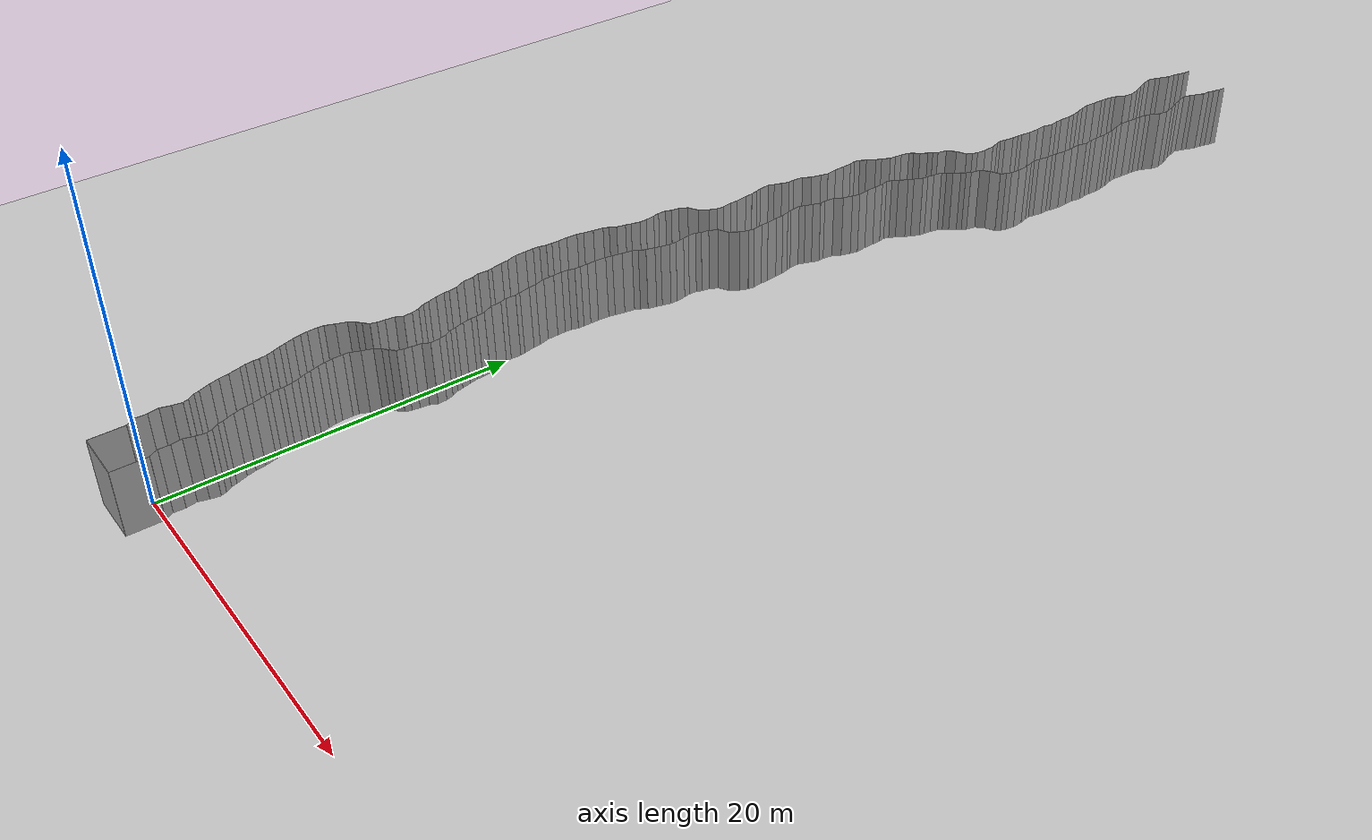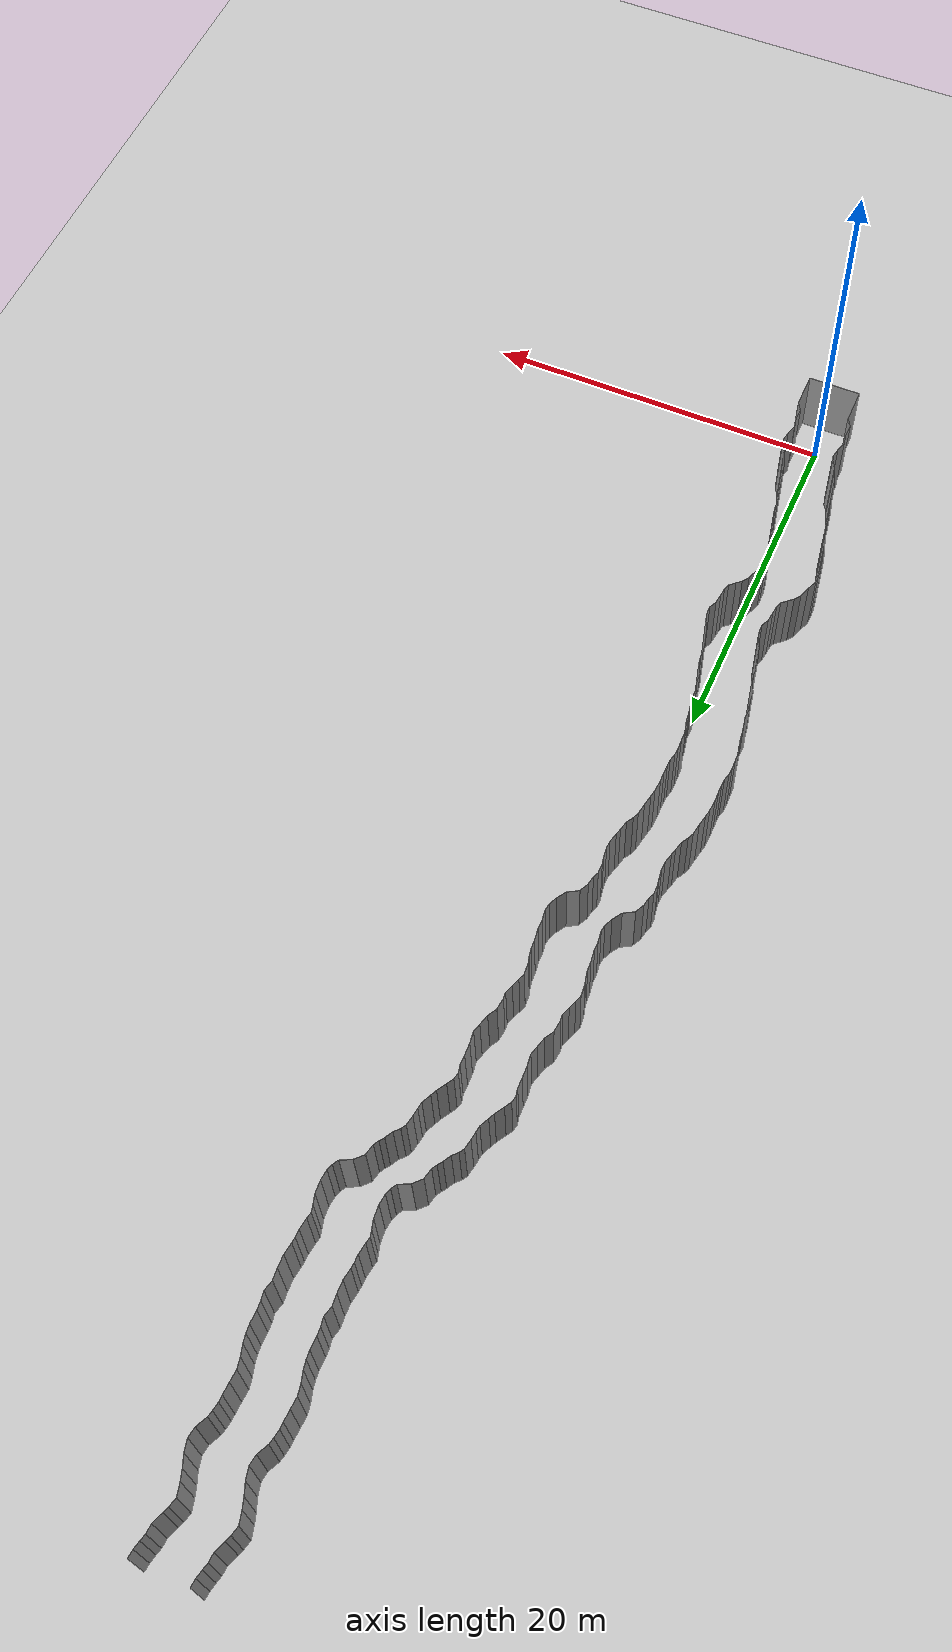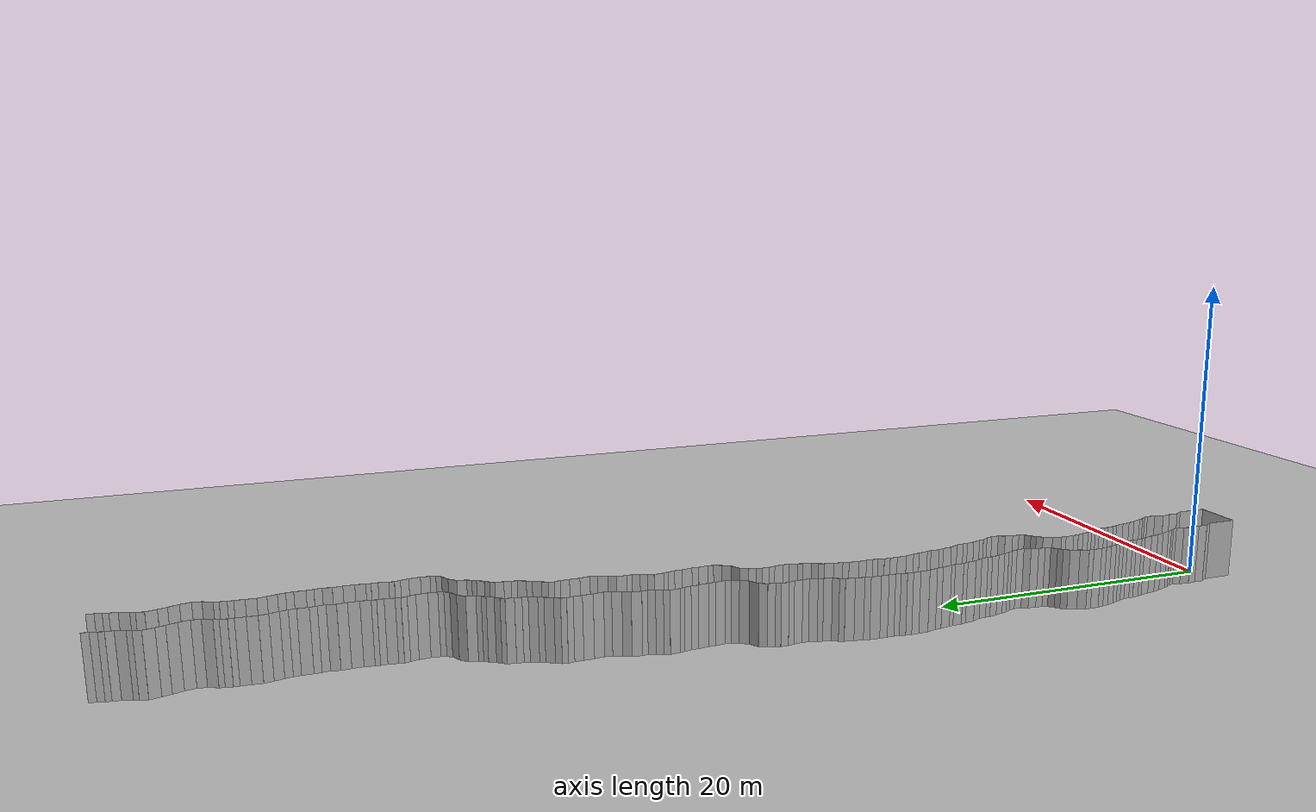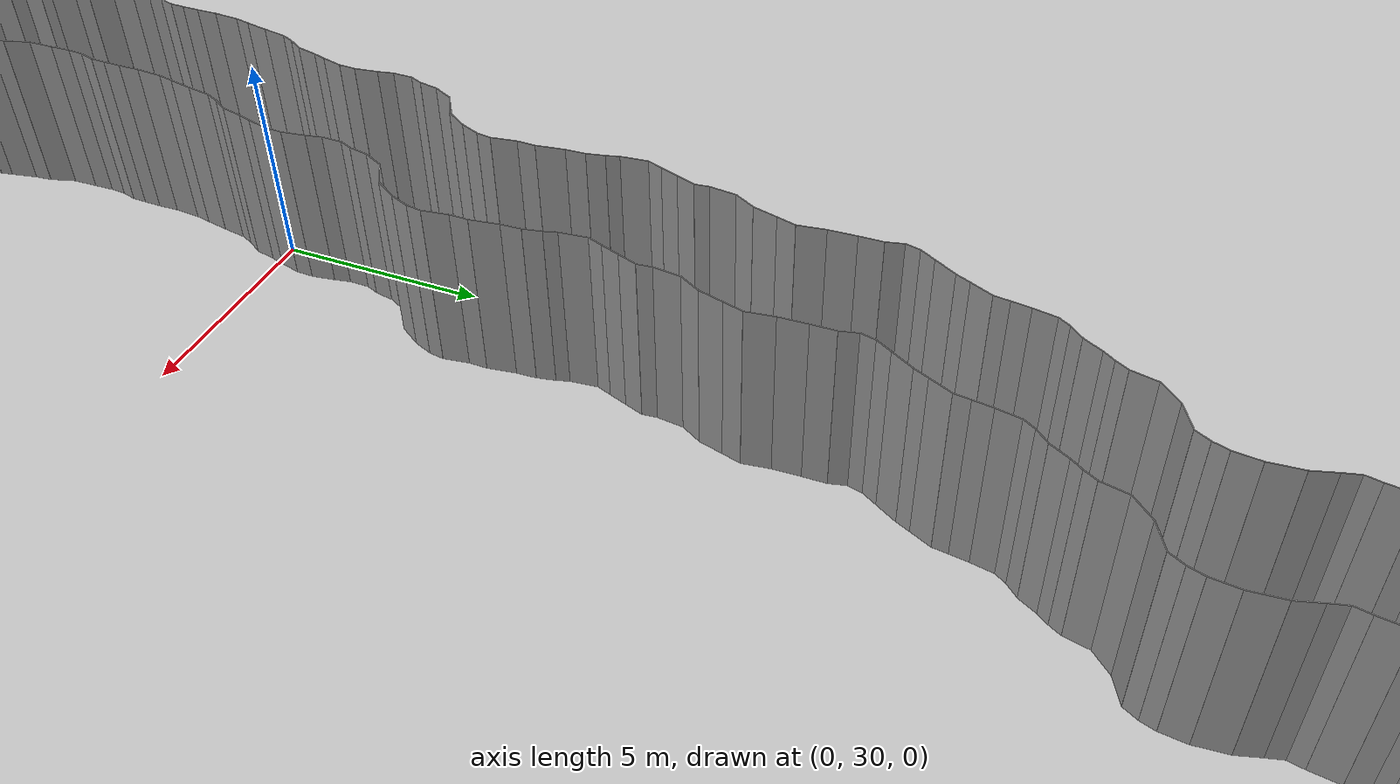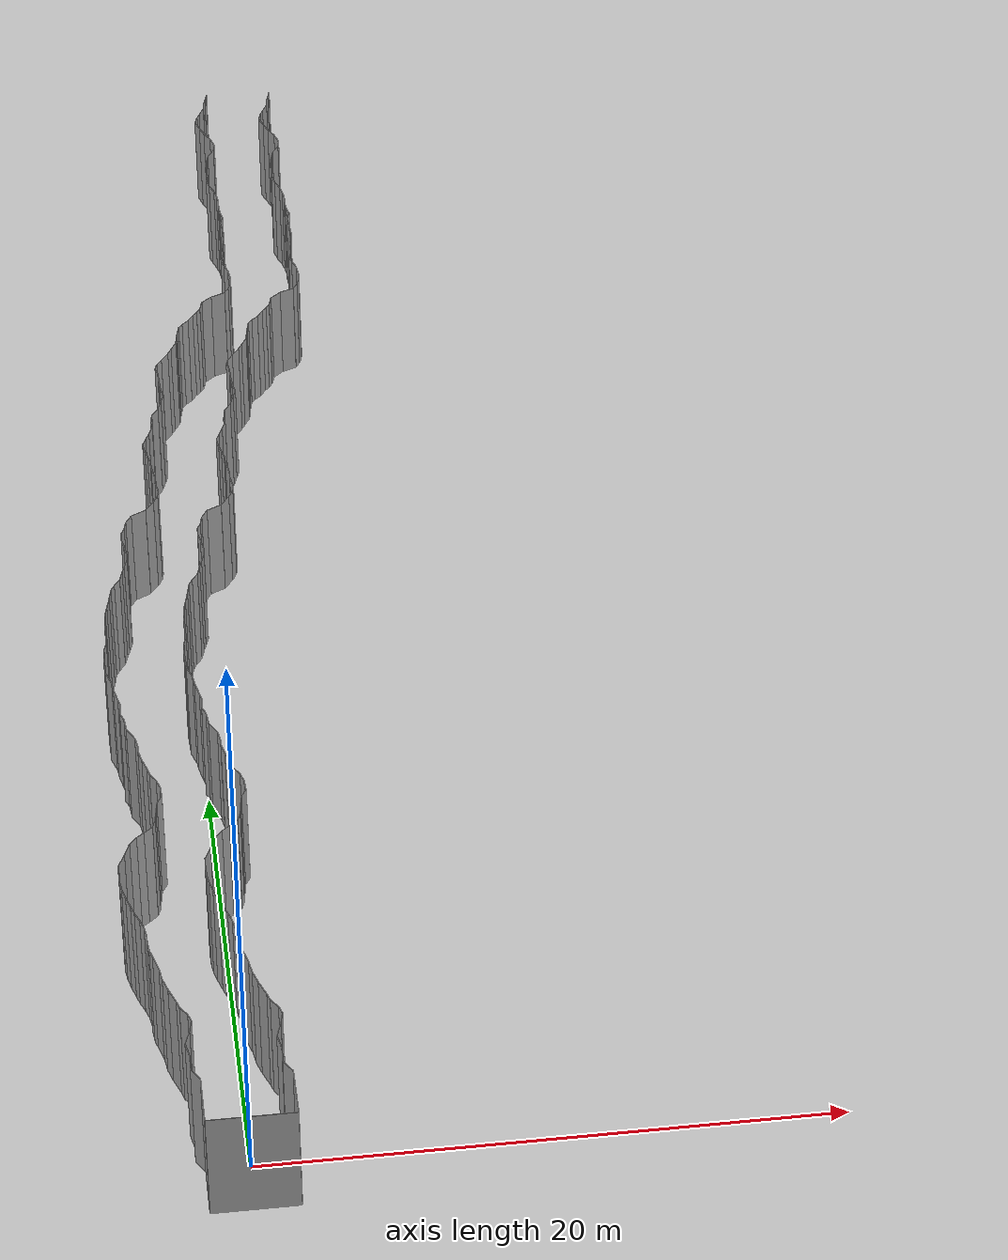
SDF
<sdf version="1.6">
 <world name="default">
  <light name="sun" type="directional">
   <pose>0 0 10 0 -0 0</pose>
   <diffuse>0.8 0.8 0.8 1</diffuse>
   <specular>0.2 0.2 0.2 1</specular>
   <attenuation>
    <range>1000</range>
    <constant>0.9</constant>
    <linear>0.01</linear>
    <quadratic>0.001</quadratic>
   </attenuation>
   <direction>-0.5 0.1 -0.9</direction>
  </light>
  <model name="ground_plane">
   <static>1</static>
   <link name="link">
    <collision name="collision">
     <geometry><plane><normal>0 0 1</normal><size>200 200</size></plane></geometry>
     <surface><friction><ode><mu>100</mu><mu2>50</mu2></ode></friction></surface>
    </collision>
    <visual name="visual">
     <cast_shadows>0</cast_shadows>
     <geometry><plane><normal>0 0 1</normal><size>200 200</size></plane></geometry>
     <material>
      <script><uri>file://media/materials/scripts/gazebo.material</uri><name>Gazebo/Grey</name></script>
     </material>
    </visual>
   </link>
   <pose>0 100 0 0 -0 0</pose>
  </model>
  <gravity>0 0 -9.8</gravity>
  <magnetic_field>6e-06 2.3e-05 -4.2e-05</magnetic_field>
  <atmosphere type="adiabatic"/>
  <physics default="0" name="default_physics" type="ode">
   <max_step_size>0.001</max_step_size>
   <real_time_factor>1</real_time_factor>
   <real_time_update_rate>1000</real_time_update_rate>
  </physics>
  <scene><ambient>0.4 0.4 0.4 1</ambient><background>0.7 0.7 0.7 1</background><shadows>1</shadows></scene>
  <spherical_coordinates>
   <surface_model>EARTH_WGS84</surface_model>
   <latitude_deg>0</latitude_deg>
   <longitude_deg>0</longitude_deg>
   <elevation>0</elevation>
   <heading_deg>0</heading_deg>
  </spherical_coordinates>
  <model name="wall_back">
   <static>1</static>
   <pose>0.0 -2 2 0.0 0 0.0</pose>
   <link name="link">
    <collision name="collision"><geometry><box><size>3 0.02 4</size></box></geometry></collision>
    <visual name="visual">
     <material>
      <script><name>Gazebo/Grey</name><uri>file://media/materials/scripts/gazebo.material</uri></script>
     </material>
     <geometry><box><size>3 0.02 4</size></box></geometry>
    </visual>
   </link>
  </model>
  <model name="wall_left">
   <static>1</static>
   <pose>1.5 -1 2 0 0 0.00</pose>
   <link name="link">
    <collision name="collision"><geometry><box><size>0.02 2 4</size></box></geometry></collision>
    <visual name="visual">
     <material>
      <script><name>Gazebo/Grey</name><uri>file://media/materials/scripts/gazebo.material</uri></script>
     </material>
     <geometry><box><size>0.02 2 4</size></box></geometry>
    </visual>
   </link>
  </model>
  <model name="wall_right">
   <static>1</static>
   <pose>-1.5 -1 2 0 0 0.00</pose>
   <link name="link">
    <collision name="collision"><geometry><box><size>0.02 2 4</size></box></geometry></collision>
    <visual name="visual">
     <material>
      <script><name>Gazebo/Grey</name><uri>file://media/materials/scripts/gazebo.material</uri></script>
     </material>
     <geometry><box><size>0.02 2 4</size></box></geometry>
    </visual>
   </link>
  </model>
  <model name="wall_0">
   <static>1</static>
   <pose>-1.646472720653088 0.2521328927211947 2 0 0 0.5262828498397113</pose>
   <link name="link">
    <collision name="collision"><geometry><box><size>0.02 0.583181801799 4</size></box></geometry></collision>
    <visual name="visual">
     <material>
      <script><name>Gazebo/Grey</name><uri>file://media/materials/scripts/gazebo.material</uri></script>
     </material>
     <geometry><box><size>0.02 0.583181801799 4</size></box></geometry>
    </visual>
   </link>
  </model>
  <model name="wall_1">
   <static>1</static>
   <pose>1.353527279346912 0.2521328927211947 2 0 0 0.5262828498397113</pose>
   <link name="link">
    <collision name="collision"><geometry><box><size>0.02 0.583181801799 4</size></box></geometry></collision>
    <visual name="visual">
     <material>
      <script><name>Gazebo/Grey</name><uri>file://media/materials/scripts/gazebo.material</uri></script>
     </material>
     <geometry><box><size>0.02 0.583181801799 4</size></box></geometry>
    </visual>
   </link>
  </model>
  <model name="wall_2">
   <static>1</static>
   <pose>-1.7805583796743014 0.8299118691459411 2 0 0 -0.03802008703757331</pose>
   <link name="link">
    <collision name="collision"><geometry><box><size>0.02 0.651763181308 4</size></box></geometry></collision>
    <visual name="visual">
     <material>
      <script><name>Gazebo/Grey</name><uri>file://media/materials/scripts/gazebo.material</uri></script>
     </material>
     <geometry><box><size>0.02 0.651763181308 4</size></box></geometry>
    </visual>
   </link>
  </model>
  <model name="wall_3">
   <static>1</static>
   <pose>1.2194416203256986 0.8299118691459411 2 0 0 -0.03802008703757331</pose>
   <link name="link">
    <collision name="collision"><geometry><box><size>0.02 0.651763181308 4</size></box></geometry></collision>
    <visual name="visual">
     <material>
      <script><name>Gazebo/Grey</name><uri>file://media/materials/scripts/gazebo.material</uri></script>
     </material>
     <geometry><box><size>0.02 0.651763181308 4</size></box></geometry>
    </visual>
   </link>
  </model>
  <model name="wall_4">
   <static>1</static>
   <pose>-1.8246142902141258 1.4657746014149375 2 0 0 0.1799781418398594</pose>
   <link name="link">
    <collision name="collision"><geometry><box><size>0.02 0.63061930879 4</size></box></geometry></collision>
    <visual name="visual">
     <material>
      <script><name>Gazebo/Grey</name><uri>file://media/materials/scripts/gazebo.material</uri></script>
     </material>
     <geometry><box><size>0.02 0.63061930879 4</size></box></geometry>
    </visual>
   </link>
  </model>
  <model name="wall_5">
   <static>1</static>
   <pose>1.1753857097858742 1.4657746014149375 2 0 0 0.1799781418398594</pose>
   <link name="link">
    <collision name="collision"><geometry><box><size>0.02 0.63061930879 4</size></box></geometry></collision>
    <visual name="visual">
     <material>
      <script><name>Gazebo/Grey</name><uri>file://media/materials/scripts/gazebo.material</uri></script>
     </material>
     <geometry><box><size>0.02 0.63061930879 4</size></box></geometry>
    </visual>
   </link>
  </model>
  <model name="wall_6">
   <static>1</static>
   <pose>-1.7928527109547967 2.067357282523565 2 0 0 -0.29395733413151454</pose>
   <link name="link">
    <collision name="collision"><geometry><box><size>0.02 0.608848775356 4</size></box></geometry></collision>
    <visual name="visual">
     <material>
      <script><name>Gazebo/Grey</name><uri>file://media/materials/scripts/gazebo.material</uri></script>
     </material>
     <geometry><box><size>0.02 0.608848775356 4</size></box></geometry>
    </visual>
   </link>
  </model>
  <model name="wall_7">
   <static>1</static>
   <pose>1.2071472890452033 2.067357282523565 2 0 0 -0.29395733413151454</pose>
   <link name="link">
    <collision name="collision"><geometry><box><size>0.02 0.608848775356 4</size></box></geometry></collision>
    <visual name="visual">
     <material>
      <script><name>Gazebo/Grey</name><uri>file://media/materials/scripts/gazebo.material</uri></script>
     </material>
     <geometry><box><size>0.02 0.608848775356 4</size></box></geometry>
    </visual>
   </link>
  </model>
  <model name="wall_8">
   <static>1</static>
   <pose>-1.654111112099372 2.636833541480434 2 0 0 -0.1797544799252827</pose>
   <link name="link">
    <collision name="collision"><geometry><box><size>0.02 0.565329253438 4</size></box></geometry></collision>
    <visual name="visual">
     <material>
      <script><name>Gazebo/Grey</name><uri>file://media/materials/scripts/gazebo.material</uri></script>
     </material>
     <geometry><box><size>0.02 0.565329253438 4</size></box></geometry>
    </visual>
   </link>
  </model>
  <model name="wall_9">
   <static>1</static>
   <pose>1.345888887900628 2.636833541480434 2 0 0 -0.1797544799252827</pose>
   <link name="link">
    <collision name="collision"><geometry><box><size>0.02 0.565329253438 4</size></box></geometry></collision>
    <visual name="visual">
     <material>
      <script><name>Gazebo/Grey</name><uri>file://media/materials/scripts/gazebo.material</uri></script>
     </material>
     <geometry><box><size>0.02 0.565329253438 4</size></box></geometry>
    </visual>
   </link>
  </model>
  <model name="wall_10">
   <static>1</static>
   <pose>-1.651624679783498 3.0721492965574253 2 0 0 0.2966365221625628</pose>
   <link name="link">
    <collision name="collision"><geometry><box><size>0.02 0.328770070746 4</size></box></geometry></collision>
    <visual name="visual">
     <material>
      <script><name>Gazebo/Grey</name><uri>file://media/materials/scripts/gazebo.material</uri></script>
     </material>
     <geometry><box><size>0.02 0.328770070746 4</size></box></geometry>
    </visual>
   </link>
  </model>
  <model name="wall_11">
   <static>1</static>
   <pose>1.348375320216502 3.0721492965574253 2 0 0 0.2966365221625628</pose>
   <link name="link">
    <collision name="collision"><geometry><box><size>0.02 0.328770070746 4</size></box></geometry></collision>
    <visual name="visual">
     <material>
      <script><name>Gazebo/Grey</name><uri>file://media/materials/scripts/gazebo.material</uri></script>
     </material>
     <geometry><box><size>0.02 0.328770070746 4</size></box></geometry>
    </visual>
   </link>
  </model>
  <model name="wall_12">
   <static>1</static>
   <pose>-1.8217730860297554 3.419943185669444 2 0 0 0.5697643503131937</pose>
   <link name="link">
    <collision name="collision"><geometry><box><size>0.02 0.452688827957 4</size></box></geometry></collision>
    <visual name="visual">
     <material>
      <script><name>Gazebo/Grey</name><uri>file://media/materials/scripts/gazebo.material</uri></script>
     </material>
     <geometry><box><size>0.02 0.452688827957 4</size></box></geometry>
    </visual>
   </link>
  </model>
  <model name="wall_13">
   <static>1</static>
   <pose>1.1782269139702446 3.419943185669444 2 0 0 0.5697643503131937</pose>
   <link name="link">
    <collision name="collision"><geometry><box><size>0.02 0.452688827957 4</size></box></geometry></collision>
    <visual name="visual">
     <material>
      <script><name>Gazebo/Grey</name><uri>file://media/materials/scripts/gazebo.material</uri></script>
     </material>
     <geometry><box><size>0.02 0.452688827957 4</size></box></geometry>
    </visual>
   </link>
  </model>
  <model name="wall_14">
   <static>1</static>
   <pose>-1.9887674820835646 3.7673717069043113 2 0 0 0.2788014066412116</pose>
   <link name="link">
    <collision name="collision"><geometry><box><size>0.02 0.326279274049 4</size></box></geometry></collision>
    <visual name="visual">
     <material>
      <script><name>Gazebo/Grey</name><uri>file://media/materials/scripts/gazebo.material</uri></script>
     </material>
     <geometry><box><size>0.02 0.326279274049 4</size></box></geometry>
    </visual>
   </link>
  </model>
  <model name="wall_15">
   <static>1</static>
   <pose>1.0112325179164354 3.7673717069043113 2 0 0 0.2788014066412116</pose>
   <link name="link">
    <collision name="collision"><geometry><box><size>0.02 0.326279274049 4</size></box></geometry></collision>
    <visual name="visual">
     <material>
      <script><name>Gazebo/Grey</name><uri>file://media/materials/scripts/gazebo.material</uri></script>
     </material>
     <geometry><box><size>0.02 0.326279274049 4</size></box></geometry>
    </visual>
   </link>
  </model>
  <model name="wall_16">
   <static>1</static>
   <pose>-2.1496737845620277 4.248490738769129 2 0 0 0.3435593770522331</pose>
   <link name="link">
    <collision name="collision"><geometry><box><size>0.02 0.688810674007 4</size></box></geometry></collision>
    <visual name="visual">
     <material>
      <script><name>Gazebo/Grey</name><uri>file://media/materials/scripts/gazebo.material</uri></script>
     </material>
     <geometry><box><size>0.02 0.688810674007 4</size></box></geometry>
    </visual>
   </link>
  </model>
  <model name="wall_17">
   <static>1</static>
   <pose>0.8503262154379723 4.248490738769129 2 0 0 0.3435593770522331</pose>
   <link name="link">
    <collision name="collision"><geometry><box><size>0.02 0.688810674007 4</size></box></geometry></collision>
    <visual name="visual">
     <material>
      <script><name>Gazebo/Grey</name><uri>file://media/materials/scripts/gazebo.material</uri></script>
     </material>
     <geometry><box><size>0.02 0.688810674007 4</size></box></geometry>
    </visual>
   </link>
  </model>
  <model name="wall_18">
   <static>1</static>
   <pose>-2.3453692192830045 4.846442544064273 2 0 0 0.28333763011179336</pose>
   <link name="link">
    <collision name="collision"><geometry><box><size>0.02 0.570076105899 4</size></box></geometry></collision>
    <visual name="visual">
     <material>
      <script><name>Gazebo/Grey</name><uri>file://media/materials/scripts/gazebo.material</uri></script>
     </material>
     <geometry><box><size>0.02 0.570076105899 4</size></box></geometry>
    </visual>
   </link>
  </model>
  <model name="wall_19">
   <static>1</static>
   <pose>0.6546307807169955 4.846442544064273 2 0 0 0.28333763011179336</pose>
   <link name="link">
    <collision name="collision"><geometry><box><size>0.02 0.570076105899 4</size></box></geometry></collision>
    <visual name="visual">
     <material>
      <script><name>Gazebo/Grey</name><uri>file://media/materials/scripts/gazebo.material</uri></script>
     </material>
     <geometry><box><size>0.02 0.570076105899 4</size></box></geometry>
    </visual>
   </link>
  </model>
  <model name="wall_20">
   <static>1</static>
   <pose>-2.464495090356621 5.401648394360598 2 0 0 0.1391848641803248</pose>
   <link name="link">
    <collision name="collision"><geometry><box><size>0.02 0.568564181072 4</size></box></geometry></collision>
    <visual name="visual">
     <material>
      <script><name>Gazebo/Grey</name><uri>file://media/materials/scripts/gazebo.material</uri></script>
     </material>
     <geometry><box><size>0.02 0.568564181072 4</size></box></geometry>
    </visual>
   </link>
  </model>
  <model name="wall_21">
   <static>1</static>
   <pose>0.5355049096433788 5.401648394360598 2 0 0 0.1391848641803248</pose>
   <link name="link">
    <collision name="collision"><geometry><box><size>0.02 0.568564181072 4</size></box></geometry></collision>
    <visual name="visual">
     <material>
      <script><name>Gazebo/Grey</name><uri>file://media/materials/scripts/gazebo.material</uri></script>
     </material>
     <geometry><box><size>0.02 0.568564181072 4</size></box></geometry>
    </visual>
   </link>
  </model>
  <model name="wall_22">
   <static>1</static>
   <pose>-2.5908645229118625 6.020460067990556 2 0 0 0.25224741727527383</pose>
   <link name="link">
    <collision name="collision"><geometry><box><size>0.02 0.696602220084 4</size></box></geometry></collision>
    <visual name="visual">
     <material>
      <script><name>Gazebo/Grey</name><uri>file://media/materials/scripts/gazebo.material</uri></script>
     </material>
     <geometry><box><size>0.02 0.696602220084 4</size></box></geometry>
    </visual>
   </link>
  </model>
  <model name="wall_23">
   <static>1</static>
   <pose>0.40913547708813747 6.020460067990556 2 0 0 0.25224741727527383</pose>
   <link name="link">
    <collision name="collision"><geometry><box><size>0.02 0.696602220084 4</size></box></geometry></collision>
    <visual name="visual">
     <material>
      <script><name>Gazebo/Grey</name><uri>file://media/materials/scripts/gazebo.material</uri></script>
     </material>
     <geometry><box><size>0.02 0.696602220084 4</size></box></geometry>
    </visual>
   </link>
  </model>
  <model name="wall_24">
   <static>1</static>
   <pose>-2.7244688160468784 6.529034117871786 2 0 0 0.2660243439465342</pose>
   <link name="link">
    <collision name="collision"><geometry><box><size>0.02 0.355081017718 4</size></box></geometry></collision>
    <visual name="visual">
     <material>
      <script><name>Gazebo/Grey</name><uri>file://media/materials/scripts/gazebo.material</uri></script>
     </material>
     <geometry><box><size>0.02 0.355081017718 4</size></box></geometry>
    </visual>
   </link>
  </model>
  <model name="wall_25">
   <static>1</static>
   <pose>0.2755311839531216 6.529034117871786 2 0 0 0.2660243439465342</pose>
   <link name="link">
    <collision name="collision"><geometry><box><size>0.02 0.355081017718 4</size></box></geometry></collision>
    <visual name="visual">
     <material>
      <script><name>Gazebo/Grey</name><uri>file://media/materials/scripts/gazebo.material</uri></script>
     </material>
     <geometry><box><size>0.02 0.355081017718 4</size></box></geometry>
    </visual>
   </link>
  </model>
  <model name="wall_26">
   <static>1</static>
   <pose>-2.7943474655296257 6.927998866993099 2 0 0 0.1015674703593804</pose>
   <link name="link">
    <collision name="collision"><geometry><box><size>0.02 0.457697678211 4</size></box></geometry></collision>
    <visual name="visual">
     <material>
      <script><name>Gazebo/Grey</name><uri>file://media/materials/scripts/gazebo.material</uri></script>
     </material>
     <geometry><box><size>0.02 0.457697678211 4</size></box></geometry>
    </visual>
   </link>
  </model>
  <model name="wall_27">
   <static>1</static>
   <pose>0.20565253447037435 6.927998866993099 2 0 0 0.1015674703593804</pose>
   <link name="link">
    <collision name="collision"><geometry><box><size>0.02 0.457697678211 4</size></box></geometry></collision>
    <visual name="visual">
     <material>
      <script><name>Gazebo/Grey</name><uri>file://media/materials/scripts/gazebo.material</uri></script>
     </material>
     <geometry><box><size>0.02 0.457697678211 4</size></box></geometry>
    </visual>
   </link>
  </model>
  <model name="wall_28">
   <static>1</static>
   <pose>-2.813771798485691 7.314480452146644 2 0 0 -0.023792948814899594</pose>
   <link name="link">
    <collision name="collision"><geometry><box><size>0.02 0.317714182185 4</size></box></geometry></collision>
    <visual name="visual">
     <material>
      <script><name>Gazebo/Grey</name><uri>file://media/materials/scripts/gazebo.material</uri></script>
     </material>
     <geometry><box><size>0.02 0.317714182185 4</size></box></geometry>
    </visual>
   </link>
  </model>
  <model name="wall_29">
   <static>1</static>
   <pose>0.18622820151430908 7.314480452146644 2 0 0 -0.023792948814899594</pose>
   <link name="link">
    <collision name="collision"><geometry><box><size>0.02 0.317714182185 4</size></box></geometry></collision>
    <visual name="visual">
     <material>
      <script><name>Gazebo/Grey</name><uri>file://media/materials/scripts/gazebo.material</uri></script>
     </material>
     <geometry><box><size>0.02 0.317714182185 4</size></box></geometry>
    </visual>
   </link>
  </model>
  <model name="wall_30">
   <static>1</static>
   <pose>-2.842885285728868 7.694288640828782 2 0 0 0.14775419900061726</pose>
   <link name="link">
    <collision name="collision"><geometry><box><size>0.02 0.44686103244 4</size></box></geometry></collision>
    <visual name="visual">
     <material>
      <script><name>Gazebo/Grey</name><uri>file://media/materials/scripts/gazebo.material</uri></script>
     </material>
     <geometry><box><size>0.02 0.44686103244 4</size></box></geometry>
    </visual>
   </link>
  </model>
  <model name="wall_31">
   <static>1</static>
   <pose>0.157114714271132 7.694288640828782 2 0 0 0.14775419900061726</pose>
   <link name="link">
    <collision name="collision"><geometry><box><size>0.02 0.44686103244 4</size></box></geometry></collision>
    <visual name="visual">
     <material>
      <script><name>Gazebo/Grey</name><uri>file://media/materials/scripts/gazebo.material</uri></script>
     </material>
     <geometry><box><size>0.02 0.44686103244 4</size></box></geometry>
    </visual>
   </link>
  </model>
  <model name="wall_32">
   <static>1</static>
   <pose>-2.937693382810968 8.119197226541164 2 0 0 0.2947896951456151</pose>
   <link name="link">
    <collision name="collision"><geometry><box><size>0.02 0.426210374705 4</size></box></geometry></collision>
    <visual name="visual">
     <material>
      <script><name>Gazebo/Grey</name><uri>file://media/materials/scripts/gazebo.material</uri></script>
     </material>
     <geometry><box><size>0.02 0.426210374705 4</size></box></geometry>
    </visual>
   </link>
  </model>
  <model name="wall_33">
   <static>1</static>
   <pose>0.062306617189031854 8.119197226541164 2 0 0 0.2947896951456151</pose>
   <link name="link">
    <collision name="collision"><geometry><box><size>0.02 0.426210374705 4</size></box></geometry></collision>
    <visual name="visual">
     <material>
      <script><name>Gazebo/Grey</name><uri>file://media/materials/scripts/gazebo.material</uri></script>
     </material>
     <geometry><box><size>0.02 0.426210374705 4</size></box></geometry>
    </visual>
   </link>
  </model>
  <model name="wall_34">
   <static>1</static>
   <pose>-3.0810454975317696 8.535709995251565 2 0 0 0.3658107050440577</pose>
   <link name="link">
    <collision name="collision"><geometry><box><size>0.02 0.455327663276 4</size></box></geometry></collision>
    <visual name="visual">
     <material>
      <script><name>Gazebo/Grey</name><uri>file://media/materials/scripts/gazebo.material</uri></script>
     </material>
     <geometry><box><size>0.02 0.455327663276 4</size></box></geometry>
    </visual>
   </link>
  </model>
  <model name="wall_35">
   <static>1</static>
   <pose>-0.0810454975317696 8.535709995251565 2 0 0 0.3658107050440577</pose>
   <link name="link">
    <collision name="collision"><geometry><box><size>0.02 0.455327663276 4</size></box></geometry></collision>
    <visual name="visual">
     <material>
      <script><name>Gazebo/Grey</name><uri>file://media/materials/scripts/gazebo.material</uri></script>
     </material>
     <geometry><box><size>0.02 0.455327663276 4</size></box></geometry>
    </visual>
   </link>
  </model>
  <model name="wall_36">
   <static>1</static>
   <pose>-3.2181885288587333 8.930879608150983 2 0 0 0.29615059662219506</pose>
   <link name="link">
    <collision name="collision"><geometry><box><size>0.02 0.381757807621 4</size></box></geometry></collision>
    <visual name="visual">
     <material>
      <script><name>Gazebo/Grey</name><uri>file://media/materials/scripts/gazebo.material</uri></script>
     </material>
     <geometry><box><size>0.02 0.381757807621 4</size></box></geometry>
    </visual>
   </link>
  </model>
  <model name="wall_37">
   <static>1</static>
   <pose>-0.2181885288587333 8.930879608150983 2 0 0 0.29615059662219506</pose>
   <link name="link">
    <collision name="collision"><geometry><box><size>0.02 0.381757807621 4</size></box></geometry></collision>
    <visual name="visual">
     <material>
      <script><name>Gazebo/Grey</name><uri>file://media/materials/scripts/gazebo.material</uri></script>
     </material>
     <geometry><box><size>0.02 0.381757807621 4</size></box></geometry>
    </visual>
   </link>
  </model>
  <model name="wall_38">
   <static>1</static>
   <pose>-3.3446470436890436 9.365705057543302 2 0 0 0.2734520063304953</pose>
   <link name="link">
    <collision name="collision"><geometry><box><size>0.02 0.523980989084 4</size></box></geometry></collision>
    <visual name="visual">
     <material>
      <script><name>Gazebo/Grey</name><uri>file://media/materials/scripts/gazebo.material</uri></script>
     </material>
     <geometry><box><size>0.02 0.523980989084 4</size></box></geometry>
    </visual>
   </link>
  </model>
  <model name="wall_39">
   <static>1</static>
   <pose>-0.34464704368904364 9.365705057543302 2 0 0 0.2734520063304953</pose>
   <link name="link">
    <collision name="collision"><geometry><box><size>0.02 0.523980989084 4</size></box></geometry></collision>
    <visual name="visual">
     <material>
      <script><name>Gazebo/Grey</name><uri>file://media/materials/scripts/gazebo.material</uri></script>
     </material>
     <geometry><box><size>0.02 0.523980989084 4</size></box></geometry>
    </visual>
   </link>
  </model>
  <model name="wall_40">
   <static>1</static>
   <pose>-3.4694642354787946 9.847987940979522 2 0 0 0.23084731840499068</pose>
   <link name="link">
    <collision name="collision"><geometry><box><size>0.02 0.472590062462 4</size></box></geometry></collision>
    <visual name="visual">
     <material>
      <script><name>Gazebo/Grey</name><uri>file://media/materials/scripts/gazebo.material</uri></script>
     </material>
     <geometry><box><size>0.02 0.472590062462 4</size></box></geometry>
    </visual>
   </link>
  </model>
  <model name="wall_41">
   <static>1</static>
   <pose>-0.46946423547879457 9.847987940979522 2 0 0 0.23084731840499068</pose>
   <link name="link">
    <collision name="collision"><geometry><box><size>0.02 0.472590062462 4</size></box></geometry></collision>
    <visual name="visual">
     <material>
      <script><name>Gazebo/Grey</name><uri>file://media/materials/scripts/gazebo.material</uri></script>
     </material>
     <geometry><box><size>0.02 0.472590062462 4</size></box></geometry>
    </visual>
   </link>
  </model>
  <model name="wall_42">
   <static>1</static>
   <pose>-3.550245482368944 10.282113419791324 2 0 0 0.13015921709245903</pose>
   <link name="link">
    <collision name="collision"><geometry><box><size>0.02 0.411679649236 4</size></box></geometry></collision>
    <visual name="visual">
     <material>
      <script><name>Gazebo/Grey</name><uri>file://media/materials/scripts/gazebo.material</uri></script>
     </material>
     <geometry><box><size>0.02 0.411679649236 4</size></box></geometry>
    </visual>
   </link>
  </model>
  <model name="wall_43">
   <static>1</static>
   <pose>-0.5502454823689442 10.282113419791324 2 0 0 0.13015921709245903</pose>
   <link name="link">
    <collision name="collision"><geometry><box><size>0.02 0.411679649236 4</size></box></geometry></collision>
    <visual name="visual">
     <material>
      <script><name>Gazebo/Grey</name><uri>file://media/materials/scripts/gazebo.material</uri></script>
     </material>
     <geometry><box><size>0.02 0.411679649236 4</size></box></geometry>
    </visual>
   </link>
  </model>
  <model name="wall_44">
   <static>1</static>
   <pose>-3.582566978388316 10.788789284754214 2 0 0 0.01852251150257199</pose>
   <link name="link">
    <collision name="collision"><geometry><box><size>0.02 0.605258203618 4</size></box></geometry></collision>
    <visual name="visual">
     <material>
      <script><name>Gazebo/Grey</name><uri>file://media/materials/scripts/gazebo.material</uri></script>
     </material>
     <geometry><box><size>0.02 0.605258203618 4</size></box></geometry>
    </visual>
   </link>
  </model>
  <model name="wall_45">
   <static>1</static>
   <pose>-0.5825669783883161 10.788789284754214 2 0 0 0.01852251150257199</pose>
   <link name="link">
    <collision name="collision"><geometry><box><size>0.02 0.605258203618 4</size></box></geometry></collision>
    <visual name="visual">
     <material>
      <script><name>Gazebo/Grey</name><uri>file://media/materials/scripts/gazebo.material</uri></script>
     </material>
     <geometry><box><size>0.02 0.605258203618 4</size></box></geometry>
    </visual>
   </link>
  </model>
  <model name="wall_46">
   <static>1</static>
   <pose>-3.580344865107751 11.264861147872066 2 0 0 -0.04508461059237172</pose>
   <link name="link">
    <collision name="collision"><geometry><box><size>0.02 0.347342294705 4</size></box></geometry></collision>
    <visual name="visual">
     <material>
      <script><name>Gazebo/Grey</name><uri>file://media/materials/scripts/gazebo.material</uri></script>
     </material>
     <geometry><box><size>0.02 0.347342294705 4</size></box></geometry>
    </visual>
   </link>
  </model>
  <model name="wall_47">
   <static>1</static>
   <pose>-0.580344865107751 11.264861147872066 2 0 0 -0.04508461059237172</pose>
   <link name="link">
    <collision name="collision"><geometry><box><size>0.02 0.347342294705 4</size></box></geometry></collision>
    <visual name="visual">
     <material>
      <script><name>Gazebo/Grey</name><uri>file://media/materials/scripts/gazebo.material</uri></script>
     </material>
     <geometry><box><size>0.02 0.347342294705 4</size></box></geometry>
    </visual>
   </link>
  </model>
  <model name="wall_48">
   <static>1</static>
   <pose>-3.4586854255687363 11.709851498230915 2 0 0 -0.39701419454328973</pose>
   <link name="link">
    <collision name="collision"><geometry><box><size>0.02 0.588787470759 4</size></box></geometry></collision>
    <visual name="visual">
     <material>
      <script><name>Gazebo/Grey</name><uri>file://media/materials/scripts/gazebo.material</uri></script>
     </material>
     <geometry><box><size>0.02 0.588787470759 4</size></box></geometry>
    </visual>
   </link>
  </model>
  <model name="wall_49">
   <static>1</static>
   <pose>-0.45868542556873626 11.709851498230915 2 0 0 -0.39701419454328973</pose>
   <link name="link">
    <collision name="collision"><geometry><box><size>0.02 0.588787470759 4</size></box></geometry></collision>
    <visual name="visual">
     <material>
      <script><name>Gazebo/Grey</name><uri>file://media/materials/scripts/gazebo.material</uri></script>
     </material>
     <geometry><box><size>0.02 0.588787470759 4</size></box></geometry>
    </visual>
   </link>
  </model>
  <model name="wall_50">
   <static>1</static>
   <pose>-3.24060932271591 12.28417778958552 2 0 0 -0.33152683761226154</pose>
   <link name="link">
    <collision name="collision"><geometry><box><size>0.02 0.640540937476 4</size></box></geometry></collision>
    <visual name="visual">
     <material>
      <script><name>Gazebo/Grey</name><uri>file://media/materials/scripts/gazebo.material</uri></script>
     </material>
     <geometry><box><size>0.02 0.640540937476 4</size></box></geometry>
    </visual>
   </link>
  </model>
  <model name="wall_51">
   <static>1</static>
   <pose>-0.24060932271591007 12.28417778958552 2 0 0 -0.33152683761226154</pose>
   <link name="link">
    <collision name="collision"><geometry><box><size>0.02 0.640540937476 4</size></box></geometry></collision>
    <visual name="visual">
     <material>
      <script><name>Gazebo/Grey</name><uri>file://media/materials/scripts/gazebo.material</uri></script>
     </material>
     <geometry><box><size>0.02 0.640540937476 4</size></box></geometry>
    </visual>
   </link>
  </model>
  <model name="wall_52">
   <static>1</static>
   <pose>-3.006086805984376 12.760769874895562 2 0 0 -0.6433445775822338</pose>
   <link name="link">
    <collision name="collision"><geometry><box><size>0.02 0.434352690442 4</size></box></geometry></collision>
    <visual name="visual">
     <material>
      <script><name>Gazebo/Grey</name><uri>file://media/materials/scripts/gazebo.material</uri></script>
     </material>
     <geometry><box><size>0.02 0.434352690442 4</size></box></geometry>
    </visual>
   </link>
  </model>
  <model name="wall_53">
   <static>1</static>
   <pose>-0.0060868059843759426 12.760769874895562 2 0 0 -0.6433445775822338</pose>
   <link name="link">
    <collision name="collision"><geometry><box><size>0.02 0.434352690442 4</size></box></geometry></collision>
    <visual name="visual">
     <material>
      <script><name>Gazebo/Grey</name><uri>file://media/materials/scripts/gazebo.material</uri></script>
     </material>
     <geometry><box><size>0.02 0.434352690442 4</size></box></geometry>
    </visual>
   </link>
  </model>
  <model name="wall_54">
   <static>1</static>
   <pose>-2.739454994831752 13.052382663313654 2 0 0 -0.8580535071223694</pose>
   <link name="link">
    <collision name="collision"><geometry><box><size>0.02 0.360450432583 4</size></box></geometry></collision>
    <visual name="visual">
     <material>
      <script><name>Gazebo/Grey</name><uri>file://media/materials/scripts/gazebo.material</uri></script>
     </material>
     <geometry><box><size>0.02 0.360450432583 4</size></box></geometry>
    </visual>
   </link>
  </model>
  <model name="wall_55">
   <static>1</static>
   <pose>0.2605450051682481 13.052382663313654 2 0 0 -0.8580535071223694</pose>
   <link name="link">
    <collision name="collision"><geometry><box><size>0.02 0.360450432583 4</size></box></geometry></collision>
    <visual name="visual">
     <material>
      <script><name>Gazebo/Grey</name><uri>file://media/materials/scripts/gazebo.material</uri></script>
     </material>
     <geometry><box><size>0.02 0.360450432583 4</size></box></geometry>
    </visual>
   </link>
  </model>
  <model name="wall_56">
   <static>1</static>
   <pose>-2.442765302182221 13.318237347946736 2 0 0 -0.8253753274017734</pose>
   <link name="link">
    <collision name="collision"><geometry><box><size>0.02 0.436407090171 4</size></box></geometry></collision>
    <visual name="visual">
     <material>
      <script><name>Gazebo/Grey</name><uri>file://media/materials/scripts/gazebo.material</uri></script>
     </material>
     <geometry><box><size>0.02 0.436407090171 4</size></box></geometry>
    </visual>
   </link>
  </model>
  <model name="wall_57">
   <static>1</static>
   <pose>0.5572346978177789 13.318237347946736 2 0 0 -0.8253753274017734</pose>
   <link name="link">
    <collision name="collision"><geometry><box><size>0.02 0.436407090171 4</size></box></geometry></collision>
    <visual name="visual">
     <material>
      <script><name>Gazebo/Grey</name><uri>file://media/materials/scripts/gazebo.material</uri></script>
     </material>
     <geometry><box><size>0.02 0.436407090171 4</size></box></geometry>
    </visual>
   </link>
  </model>
  <model name="wall_58">
   <static>1</static>
   <pose>-2.2282351430202145 13.647066206327143 2 0 0 -0.2911829039636237</pose>
   <link name="link">
    <collision name="collision"><geometry><box><size>0.02 0.377543703002 4</size></box></geometry></collision>
    <visual name="visual">
     <material>
      <script><name>Gazebo/Grey</name><uri>file://media/materials/scripts/gazebo.material</uri></script>
     </material>
     <geometry><box><size>0.02 0.377543703002 4</size></box></geometry>
    </visual>
   </link>
  </model>
  <model name="wall_59">
   <static>1</static>
   <pose>0.7717648569797855 13.647066206327143 2 0 0 -0.2911829039636237</pose>
   <link name="link">
    <collision name="collision"><geometry><box><size>0.02 0.377543703002 4</size></box></geometry></collision>
    <visual name="visual">
     <material>
      <script><name>Gazebo/Grey</name><uri>file://media/materials/scripts/gazebo.material</uri></script>
     </material>
     <geometry><box><size>0.02 0.377543703002 4</size></box></geometry>
    </visual>
   </link>
  </model>
  <model name="wall_60">
   <static>1</static>
   <pose>-2.1481181544354944 14.05162863291459 2 0 0 -0.11535083121705701</pose>
   <link name="link">
    <collision name="collision"><geometry><box><size>0.02 0.450467467456 4</size></box></geometry></collision>
    <visual name="visual">
     <material>
      <script><name>Gazebo/Grey</name><uri>file://media/materials/scripts/gazebo.material</uri></script>
     </material>
     <geometry><box><size>0.02 0.450467467456 4</size></box></geometry>
    </visual>
   </link>
  </model>
  <model name="wall_61">
   <static>1</static>
   <pose>0.8518818455645056 14.05162863291459 2 0 0 -0.11535083121705701</pose>
   <link name="link">
    <collision name="collision"><geometry><box><size>0.02 0.450467467456 4</size></box></geometry></collision>
    <visual name="visual">
     <material>
      <script><name>Gazebo/Grey</name><uri>file://media/materials/scripts/gazebo.material</uri></script>
     </material>
     <geometry><box><size>0.02 0.450467467456 4</size></box></geometry>
    </visual>
   </link>
  </model>
  <model name="wall_62">
   <static>1</static>
   <pose>-2.0886561671691704 14.541182804408542 2 0 0 -0.12550870203060424</pose>
   <link name="link">
    <collision name="collision"><geometry><box><size>0.02 0.535849401125 4</size></box></geometry></collision>
    <visual name="visual">
     <material>
      <script><name>Gazebo/Grey</name><uri>file://media/materials/scripts/gazebo.material</uri></script>
     </material>
     <geometry><box><size>0.02 0.535849401125 4</size></box></geometry>
    </visual>
   </link>
  </model>
  <model name="wall_63">
   <static>1</static>
   <pose>0.9113438328308296 14.541182804408542 2 0 0 -0.12550870203060424</pose>
   <link name="link">
    <collision name="collision"><geometry><box><size>0.02 0.535849401125 4</size></box></geometry></collision>
    <visual name="visual">
     <material>
      <script><name>Gazebo/Grey</name><uri>file://media/materials/scripts/gazebo.material</uri></script>
     </material>
     <geometry><box><size>0.02 0.535849401125 4</size></box></geometry>
    </visual>
   </link>
  </model>
  <model name="wall_64">
   <static>1</static>
   <pose>-1.9539096341268596 15.012771359049564 2 0 0 -0.4571034165402817</pose>
   <link name="link">
    <collision name="collision"><geometry><box><size>0.02 0.458627813122 4</size></box></geometry></collision>
    <visual name="visual">
     <material>
      <script><name>Gazebo/Grey</name><uri>file://media/materials/scripts/gazebo.material</uri></script>
     </material>
     <geometry><box><size>0.02 0.458627813122 4</size></box></geometry>
    </visual>
   </link>
  </model>
  <model name="wall_65">
   <static>1</static>
   <pose>1.0460903658731404 15.012771359049564 2 0 0 -0.4571034165402817</pose>
   <link name="link">
    <collision name="collision"><geometry><box><size>0.02 0.458627813122 4</size></box></geometry></collision>
    <visual name="visual">
     <material>
      <script><name>Gazebo/Grey</name><uri>file://media/materials/scripts/gazebo.material</uri></script>
     </material>
     <geometry><box><size>0.02 0.458627813122 4</size></box></geometry>
    </visual>
   </link>
  </model>
  <model name="wall_66">
   <static>1</static>
   <pose>-1.8628098846125098 15.480112977974345 2 0 0 0.03862475835284269</pose>
   <link name="link">
    <collision name="collision"><geometry><box><size>0.02 0.523531072878 4</size></box></geometry></collision>
    <visual name="visual">
     <material>
      <script><name>Gazebo/Grey</name><uri>file://media/materials/scripts/gazebo.material</uri></script>
     </material>
     <geometry><box><size>0.02 0.523531072878 4</size></box></geometry>
    </visual>
   </link>
  </model>
  <model name="wall_67">
   <static>1</static>
   <pose>1.1371901153874902 15.480112977974345 2 0 0 0.03862475835284269</pose>
   <link name="link">
    <collision name="collision"><geometry><box><size>0.02 0.523531072878 4</size></box></geometry></collision>
    <visual name="visual">
     <material>
      <script><name>Gazebo/Grey</name><uri>file://media/materials/scripts/gazebo.material</uri></script>
     </material>
     <geometry><box><size>0.02 0.523531072878 4</size></box></geometry>
    </visual>
   </link>
  </model>
  <model name="wall_68">
   <static>1</static>
   <pose>-1.931021199458651 15.959623327962316 2 0 0 0.2605417813915949</pose>
   <link name="link">
    <collision name="collision"><geometry><box><size>0.02 0.451104630185 4</size></box></geometry></collision>
    <visual name="visual">
     <material>
      <script><name>Gazebo/Grey</name><uri>file://media/materials/scripts/gazebo.material</uri></script>
     </material>
     <geometry><box><size>0.02 0.451104630185 4</size></box></geometry>
    </visual>
   </link>
  </model>
  <model name="wall_69">
   <static>1</static>
   <pose>1.068978800541349 15.959623327962316 2 0 0 0.2605417813915949</pose>
   <link name="link">
    <collision name="collision"><geometry><box><size>0.02 0.451104630185 4</size></box></geometry></collision>
    <visual name="visual">
     <material>
      <script><name>Gazebo/Grey</name><uri>file://media/materials/scripts/gazebo.material</uri></script>
     </material>
     <geometry><box><size>0.02 0.451104630185 4</size></box></geometry>
    </visual>
   </link>
  </model>
  <model name="wall_70">
   <static>1</static>
   <pose>-2.0976159528118337 16.381046465872352 2 0 0 0.4898319808032977</pose>
   <link name="link">
    <collision name="collision"><geometry><box><size>0.02 0.46119750564 4</size></box></geometry></collision>
    <visual name="visual">
     <material>
      <script><name>Gazebo/Grey</name><uri>file://media/materials/scripts/gazebo.material</uri></script>
     </material>
     <geometry><box><size>0.02 0.46119750564 4</size></box></geometry>
    </visual>
   </link>
  </model>
  <model name="wall_71">
   <static>1</static>
   <pose>0.9023840471881663 16.381046465872352 2 0 0 0.4898319808032977</pose>
   <link name="link">
    <collision name="collision"><geometry><box><size>0.02 0.46119750564 4</size></box></geometry></collision>
    <visual name="visual">
     <material>
      <script><name>Gazebo/Grey</name><uri>file://media/materials/scripts/gazebo.material</uri></script>
     </material>
     <geometry><box><size>0.02 0.46119750564 4</size></box></geometry>
    </visual>
   </link>
  </model>
  <model name="wall_72">
   <static>1</static>
   <pose>-2.2449225391340746 16.759949421015538 2 0 0 0.21776068323996245</pose>
   <link name="link">
    <collision name="collision"><geometry><box><size>0.02 0.359325681317 4</size></box></geometry></collision>
    <visual name="visual">
     <material>
      <script><name>Gazebo/Grey</name><uri>file://media/materials/scripts/gazebo.material</uri></script>
     </material>
     <geometry><box><size>0.02 0.359325681317 4</size></box></geometry>
    </visual>
   </link>
  </model>
  <model name="wall_73">
   <static>1</static>
   <pose>0.7550774608659254 16.759949421015538 2 0 0 0.21776068323996245</pose>
   <link name="link">
    <collision name="collision"><geometry><box><size>0.02 0.359325681317 4</size></box></geometry></collision>
    <visual name="visual">
     <material>
      <script><name>Gazebo/Grey</name><uri>file://media/materials/scripts/gazebo.material</uri></script>
     </material>
     <geometry><box><size>0.02 0.359325681317 4</size></box></geometry>
    </visual>
   </link>
  </model>
  <model name="wall_74">
   <static>1</static>
   <pose>-2.3580878478650598 17.201675022491074 2 0 0 0.2722587550987722</pose>
   <link name="link">
    <collision name="collision"><geometry><box><size>0.02 0.552979956595 4</size></box></geometry></collision>
    <visual name="visual">
     <material>
      <script><name>Gazebo/Grey</name><uri>file://media/materials/scripts/gazebo.material</uri></script>
     </material>
     <geometry><box><size>0.02 0.552979956595 4</size></box></geometry>
    </visual>
   </link>
  </model>
  <model name="wall_75">
   <static>1</static>
   <pose>0.6419121521349402 17.201675022491074 2 0 0 0.2722587550987722</pose>
   <link name="link">
    <collision name="collision"><geometry><box><size>0.02 0.552979956595 4</size></box></geometry></collision>
    <visual name="visual">
     <material>
      <script><name>Gazebo/Grey</name><uri>file://media/materials/scripts/gazebo.material</uri></script>
     </material>
     <geometry><box><size>0.02 0.552979956595 4</size></box></geometry>
    </visual>
   </link>
  </model>
  <model name="wall_76">
   <static>1</static>
   <pose>-2.4879441324434226 17.73647820993353 2 0 0 0.20385657502360116</pose>
   <link name="link">
    <collision name="collision"><geometry><box><size>0.02 0.548349519776 4</size></box></geometry></collision>
    <visual name="visual">
     <material>
      <script><name>Gazebo/Grey</name><uri>file://media/materials/scripts/gazebo.material</uri></script>
     </material>
     <geometry><box><size>0.02 0.548349519776 4</size></box></geometry>
    </visual>
   </link>
  </model>
  <model name="wall_77">
   <static>1</static>
   <pose>0.5120558675565774 17.73647820993353 2 0 0 0.20385657502360116</pose>
   <link name="link">
    <collision name="collision"><geometry><box><size>0.02 0.548349519776 4</size></box></geometry></collision>
    <visual name="visual">
     <material>
      <script><name>Gazebo/Grey</name><uri>file://media/materials/scripts/gazebo.material</uri></script>
     </material>
     <geometry><box><size>0.02 0.548349519776 4</size></box></geometry>
    </visual>
   </link>
  </model>
  <model name="wall_78">
   <static>1</static>
   <pose>-2.53915870391547 18.161688756901018 2 0 0 -0.027377183669309108</pose>
   <link name="link">
    <collision name="collision"><geometry><box><size>0.02 0.313543683075 4</size></box></geometry></collision>
    <visual name="visual">
     <material>
      <script><name>Gazebo/Grey</name><uri>file://media/materials/scripts/gazebo.material</uri></script>
     </material>
     <geometry><box><size>0.02 0.313543683075 4</size></box></geometry>
    </visual>
   </link>
  </model>
  <model name="wall_79">
   <static>1</static>
   <pose>0.46084129608453006 18.161688756901018 2 0 0 -0.027377183669309108</pose>
   <link name="link">
    <collision name="collision"><geometry><box><size>0.02 0.313543683075 4</size></box></geometry></collision>
    <visual name="visual">
     <material>
      <script><name>Gazebo/Grey</name><uri>file://media/materials/scripts/gazebo.material</uri></script>
     </material>
     <geometry><box><size>0.02 0.313543683075 4</size></box></geometry>
    </visual>
   </link>
  </model>
  <model name="wall_80">
   <static>1</static>
   <pose>-2.573424783727916 18.57162538054854 2 0 0 0.15110604399465902</pose>
   <link name="link">
    <collision name="collision"><geometry><box><size>0.02 0.51228444389 4</size></box></geometry></collision>
    <visual name="visual">
     <material>
      <script><name>Gazebo/Grey</name><uri>file://media/materials/scripts/gazebo.material</uri></script>
     </material>
     <geometry><box><size>0.02 0.51228444389 4</size></box></geometry>
    </visual>
   </link>
  </model>
  <model name="wall_81">
   <static>1</static>
   <pose>0.42657521627208395 18.57162538054854 2 0 0 0.15110604399465902</pose>
   <link name="link">
    <collision name="collision"><geometry><box><size>0.02 0.51228444389 4</size></box></geometry></collision>
    <visual name="visual">
     <material>
      <script><name>Gazebo/Grey</name><uri>file://media/materials/scripts/gazebo.material</uri></script>
     </material>
     <geometry><box><size>0.02 0.51228444389 4</size></box></geometry>
    </visual>
   </link>
  </model>
  <model name="wall_82">
   <static>1</static>
   <pose>-2.7519881979428247 19.118807327787838 2 0 0 0.4444904747670683</pose>
   <link name="link">
    <collision name="collision"><geometry><box><size>0.02 0.651193375674 4</size></box></geometry></collision>
    <visual name="visual">
     <material>
      <script><name>Gazebo/Grey</name><uri>file://media/materials/scripts/gazebo.material</uri></script>
     </material>
     <geometry><box><size>0.02 0.651193375674 4</size></box></geometry>
    </visual>
   </link>
  </model>
  <model name="wall_83">
   <static>1</static>
   <pose>0.24801180205717532 19.118807327787838 2 0 0 0.4444904747670683</pose>
   <link name="link">
    <collision name="collision"><geometry><box><size>0.02 0.651193375674 4</size></box></geometry></collision>
    <visual name="visual">
     <material>
      <script><name>Gazebo/Grey</name><uri>file://media/materials/scripts/gazebo.material</uri></script>
     </material>
     <geometry><box><size>0.02 0.651193375674 4</size></box></geometry>
    </visual>
   </link>
  </model>
  <model name="wall_84">
   <static>1</static>
   <pose>-2.9184482682267223 19.72543154447419 2 0 0 0.08440742873577052</pose>
   <link name="link">
    <collision name="collision"><geometry><box><size>0.02 0.627565853117 4</size></box></geometry></collision>
    <visual name="visual">
     <material>
      <script><name>Gazebo/Grey</name><uri>file://media/materials/scripts/gazebo.material</uri></script>
     </material>
     <geometry><box><size>0.02 0.627565853117 4</size></box></geometry>
    </visual>
   </link>
  </model>
  <model name="wall_85">
   <static>1</static>
   <pose>0.08155173177327768 19.72543154447419 2 0 0 0.08440742873577052</pose>
   <link name="link">
    <collision name="collision"><geometry><box><size>0.02 0.627565853117 4</size></box></geometry></collision>
    <visual name="visual">
     <material>
      <script><name>Gazebo/Grey</name><uri>file://media/materials/scripts/gazebo.material</uri></script>
     </material>
     <geometry><box><size>0.02 0.627565853117 4</size></box></geometry>
    </visual>
   </link>
  </model>
  <model name="wall_86">
   <static>1</static>
   <pose>-3.0103802036234923 20.224765987854678 2 0 0 0.3373606412311</pose>
   <link name="link">
    <collision name="collision"><geometry><box><size>0.02 0.395638827299 4</size></box></geometry></collision>
    <visual name="visual">
     <material>
      <script><name>Gazebo/Grey</name><uri>file://media/materials/scripts/gazebo.material</uri></script>
     </material>
     <geometry><box><size>0.02 0.395638827299 4</size></box></geometry>
    </visual>
   </link>
  </model>
  <model name="wall_87">
   <static>1</static>
   <pose>-0.010380203623492346 20.224765987854678 2 0 0 0.3373606412311</pose>
   <link name="link">
    <collision name="collision"><geometry><box><size>0.02 0.395638827299 4</size></box></geometry></collision>
    <visual name="visual">
     <material>
      <script><name>Gazebo/Grey</name><uri>file://media/materials/scripts/gazebo.material</uri></script>
     </material>
     <geometry><box><size>0.02 0.395638827299 4</size></box></geometry>
    </visual>
   </link>
  </model>
  <model name="wall_88">
   <static>1</static>
   <pose>-3.0590614660273667 20.705230304146117 2 0 0 -0.05710852619003276</pose>
   <link name="link">
    <collision name="collision"><geometry><box><size>0.02 0.588550827933 4</size></box></geometry></collision>
    <visual name="visual">
     <material>
      <script><name>Gazebo/Grey</name><uri>file://media/materials/scripts/gazebo.material</uri></script>
     </material>
     <geometry><box><size>0.02 0.588550827933 4</size></box></geometry>
    </visual>
   </link>
  </model>
  <model name="wall_89">
   <static>1</static>
   <pose>-0.05906146602736673 20.705230304146117 2 0 0 -0.05710852619003276</pose>
   <link name="link">
    <collision name="collision"><geometry><box><size>0.02 0.588550827933 4</size></box></geometry></collision>
    <visual name="visual">
     <material>
      <script><name>Gazebo/Grey</name><uri>file://media/materials/scripts/gazebo.material</uri></script>
     </material>
     <geometry><box><size>0.02 0.588550827933 4</size></box></geometry>
    </visual>
   </link>
  </model>
  <model name="wall_90">
   <static>1</static>
   <pose>-3.0735588118573456 21.148337560839384 2 0 0 0.20659712142865527</pose>
   <link name="link">
    <collision name="collision"><geometry><box><size>0.02 0.305111483007 4</size></box></geometry></collision>
    <visual name="visual">
     <material>
      <script><name>Gazebo/Grey</name><uri>file://media/materials/scripts/gazebo.material</uri></script>
     </material>
     <geometry><box><size>0.02 0.305111483007 4</size></box></geometry>
    </visual>
   </link>
  </model>
  <model name="wall_91">
   <static>1</static>
   <pose>-0.07355881185734559 21.148337560839384 2 0 0 0.20659712142865527</pose>
   <link name="link">
    <collision name="collision"><geometry><box><size>0.02 0.305111483007 4</size></box></geometry></collision>
    <visual name="visual">
     <material>
      <script><name>Gazebo/Grey</name><uri>file://media/materials/scripts/gazebo.material</uri></script>
     </material>
     <geometry><box><size>0.02 0.305111483007 4</size></box></geometry>
    </visual>
   </link>
  </model>
  <model name="wall_92">
   <static>1</static>
   <pose>-3.172111809200735 21.633806882878694 2 0 0 0.19747451174473082</pose>
   <link name="link">
    <collision name="collision"><geometry><box><size>0.02 0.685640773296 4</size></box></geometry></collision>
    <visual name="visual">
     <material>
      <script><name>Gazebo/Grey</name><uri>file://media/materials/scripts/gazebo.material</uri></script>
     </material>
     <geometry><box><size>0.02 0.685640773296 4</size></box></geometry>
    </visual>
   </link>
  </model>
  <model name="wall_93">
   <static>1</static>
   <pose>-0.172111809200735 21.633806882878694 2 0 0 0.19747451174473082</pose>
   <link name="link">
    <collision name="collision"><geometry><box><size>0.02 0.685640773296 4</size></box></geometry></collision>
    <visual name="visual">
     <material>
      <script><name>Gazebo/Grey</name><uri>file://media/materials/scripts/gazebo.material</uri></script>
     </material>
     <geometry><box><size>0.02 0.685640773296 4</size></box></geometry>
    </visual>
   </link>
  </model>
  <model name="wall_94">
   <static>1</static>
   <pose>-3.260638031250036 22.18285722947107 2 0 0 0.09956545866144452</pose>
   <link name="link">
    <collision name="collision"><geometry><box><size>0.02 0.427904435598 4</size></box></geometry></collision>
    <visual name="visual">
     <material>
      <script><name>Gazebo/Grey</name><uri>file://media/materials/scripts/gazebo.material</uri></script>
     </material>
     <geometry><box><size>0.02 0.427904435598 4</size></box></geometry>
    </visual>
   </link>
  </model>
  <model name="wall_95">
   <static>1</static>
   <pose>-0.26063803125003604 22.18285722947107 2 0 0 0.09956545866144452</pose>
   <link name="link">
    <collision name="collision"><geometry><box><size>0.02 0.427904435598 4</size></box></geometry></collision>
    <visual name="visual">
     <material>
      <script><name>Gazebo/Grey</name><uri>file://media/materials/scripts/gazebo.material</uri></script>
     </material>
     <geometry><box><size>0.02 0.427904435598 4</size></box></geometry>
    </visual>
   </link>
  </model>
  <model name="wall_96">
   <static>1</static>
   <pose>-3.37559019041575 22.713039445539632 2 0 0 0.28710877245513095</pose>
   <link name="link">
    <collision name="collision"><geometry><box><size>0.02 0.661663328301 4</size></box></geometry></collision>
    <visual name="visual">
     <material>
      <script><name>Gazebo/Grey</name><uri>file://media/materials/scripts/gazebo.material</uri></script>
     </material>
     <geometry><box><size>0.02 0.661663328301 4</size></box></geometry>
    </visual>
   </link>
  </model>
  <model name="wall_97">
   <static>1</static>
   <pose>-0.37559019041575015 22.713039445539632 2 0 0 0.28710877245513095</pose>
   <link name="link">
    <collision name="collision"><geometry><box><size>0.02 0.661663328301 4</size></box></geometry></collision>
    <visual name="visual">
     <material>
      <script><name>Gazebo/Grey</name><uri>file://media/materials/scripts/gazebo.material</uri></script>
     </material>
     <geometry><box><size>0.02 0.661663328301 4</size></box></geometry>
    </visual>
   </link>
  </model>
  <model name="wall_98">
   <static>1</static>
   <pose>-3.4765655600204584 23.350627148155734 2 0 0 0.022757001247260777</pose>
   <link name="link">
    <collision name="collision"><geometry><box><size>0.02 0.640762104032 4</size></box></geometry></collision>
    <visual name="visual">
     <material>
      <script><name>Gazebo/Grey</name><uri>file://media/materials/scripts/gazebo.material</uri></script>
     </material>
     <geometry><box><size>0.02 0.640762104032 4</size></box></geometry>
    </visual>
   </link>
  </model>
  <model name="wall_99">
   <static>1</static>
   <pose>-0.47656556002045836 23.350627148155734 2 0 0 0.022757001247260777</pose>
   <link name="link">
    <collision name="collision"><geometry><box><size>0.02 0.640762104032 4</size></box></geometry></collision>
    <visual name="visual">
     <material>
      <script><name>Gazebo/Grey</name><uri>file://media/materials/scripts/gazebo.material</uri></script>
     </material>
     <geometry><box><size>0.02 0.640762104032 4</size></box></geometry>
    </visual>
   </link>
  </model>
  <model name="wall_100">
   <static>1</static>
   <pose>-3.4926785539419574 23.92471308522436 2 0 0 0.0347501264575898</pose>
   <link name="link">
    <collision name="collision"><geometry><box><size>0.02 0.507882303425 4</size></box></geometry></collision>
    <visual name="visual">
     <material>
      <script><name>Gazebo/Grey</name><uri>file://media/materials/scripts/gazebo.material</uri></script>
     </material>
     <geometry><box><size>0.02 0.507882303425 4</size></box></geometry>
    </visual>
   </link>
  </model>
  <model name="wall_101">
   <static>1</static>
   <pose>-0.49267855394195736 23.92471308522436 2 0 0 0.0347501264575898</pose>
   <link name="link">
    <collision name="collision"><geometry><box><size>0.02 0.507882303425 4</size></box></geometry></collision>
    <visual name="visual">
     <material>
      <script><name>Gazebo/Grey</name><uri>file://media/materials/scripts/gazebo.material</uri></script>
     </material>
     <geometry><box><size>0.02 0.507882303425 4</size></box></geometry>
    </visual>
   </link>
  </model>
  <model name="wall_102">
   <static>1</static>
   <pose>-3.4880060224781717 24.378263700243625 2 0 0 -0.06745385195750807</pose>
   <link name="link">
    <collision name="collision"><geometry><box><size>0.02 0.400436199218 4</size></box></geometry></collision>
    <visual name="visual">
     <material>
      <script><name>Gazebo/Grey</name><uri>file://media/materials/scripts/gazebo.material</uri></script>
     </material>
     <geometry><box><size>0.02 0.400436199218 4</size></box></geometry>
    </visual>
   </link>
  </model>
  <model name="wall_103">
   <static>1</static>
   <pose>-0.4880060224781717 24.378263700243625 2 0 0 -0.06745385195750807</pose>
   <link name="link">
    <collision name="collision"><geometry><box><size>0.02 0.400436199218 4</size></box></geometry></collision>
    <visual name="visual">
     <material>
      <script><name>Gazebo/Grey</name><uri>file://media/materials/scripts/gazebo.material</uri></script>
     </material>
     <geometry><box><size>0.02 0.400436199218 4</size></box></geometry>
    </visual>
   </link>
  </model>
  <model name="wall_104">
   <static>1</static>
   <pose>-3.4211406904779946 24.769253763773005 2 0 0 -0.27216691738547527</pose>
   <link name="link">
    <collision name="collision"><geometry><box><size>0.02 0.397070486104 4</size></box></geometry></collision>
    <visual name="visual">
     <material>
      <script><name>Gazebo/Grey</name><uri>file://media/materials/scripts/gazebo.material</uri></script>
     </material>
     <geometry><box><size>0.02 0.397070486104 4</size></box></geometry>
    </visual>
   </link>
  </model>
  <model name="wall_105">
   <static>1</static>
   <pose>-0.42114069047799463 24.769253763773005 2 0 0 -0.27216691738547527</pose>
   <link name="link">
    <collision name="collision"><geometry><box><size>0.02 0.397070486104 4</size></box></geometry></collision>
    <visual name="visual">
     <material>
      <script><name>Gazebo/Grey</name><uri>file://media/materials/scripts/gazebo.material</uri></script>
     </material>
     <geometry><box><size>0.02 0.397070486104 4</size></box></geometry>
    </visual>
   </link>
  </model>
  <model name="wall_106">
   <static>1</static>
   <pose>-3.3622685841015447 25.1434598851362 2 0 0 -0.03006008768025267</pose>
   <link name="link">
    <collision name="collision"><geometry><box><size>0.02 0.366123067038 4</size></box></geometry></collision>
    <visual name="visual">
     <material>
      <script><name>Gazebo/Grey</name><uri>file://media/materials/scripts/gazebo.material</uri></script>
     </material>
     <geometry><box><size>0.02 0.366123067038 4</size></box></geometry>
    </visual>
   </link>
  </model>
  <model name="wall_107">
   <static>1</static>
   <pose>-0.3622685841015447 25.1434598851362 2 0 0 -0.03006008768025267</pose>
   <link name="link">
    <collision name="collision"><geometry><box><size>0.02 0.366123067038 4</size></box></geometry></collision>
    <visual name="visual">
     <material>
      <script><name>Gazebo/Grey</name><uri>file://media/materials/scripts/gazebo.material</uri></script>
     </material>
     <geometry><box><size>0.02 0.366123067038 4</size></box></geometry>
    </visual>
   </link>
  </model>
  <model name="wall_108">
   <static>1</static>
   <pose>-3.3534130535216713 25.551516314463214 2 0 0 -0.014898263752222586</pose>
   <link name="link">
    <collision name="collision"><geometry><box><size>0.02 0.450205157639 4</size></box></geometry></collision>
    <visual name="visual">
     <material>
      <script><name>Gazebo/Grey</name><uri>file://media/materials/scripts/gazebo.material</uri></script>
     </material>
     <geometry><box><size>0.02 0.450205157639 4</size></box></geometry>
    </visual>
   </link>
  </model>
  <model name="wall_109">
   <static>1</static>
   <pose>-0.3534130535216713 25.551516314463214 2 0 0 -0.014898263752222586</pose>
   <link name="link">
    <collision name="collision"><geometry><box><size>0.02 0.450205157639 4</size></box></geometry></collision>
    <visual name="visual">
     <material>
      <script><name>Gazebo/Grey</name><uri>file://media/materials/scripts/gazebo.material</uri></script>
     </material>
     <geometry><box><size>0.02 0.450205157639 4</size></box></geometry>
    </visual>
   </link>
  </model>
  <model name="wall_110">
   <static>1</static>
   <pose>-3.356392899036975 26.041410473022033 2 0 0 0.02391146507970312</pose>
   <link name="link">
    <collision name="collision"><geometry><box><size>0.02 0.529784569041 4</size></box></geometry></collision>
    <visual name="visual">
     <material>
      <script><name>Gazebo/Grey</name><uri>file://media/materials/scripts/gazebo.material</uri></script>
     </material>
     <geometry><box><size>0.02 0.529784569041 4</size></box></geometry>
    </visual>
   </link>
  </model>
  <model name="wall_111">
   <static>1</static>
   <pose>-0.35639289903697513 26.041410473022033 2 0 0 0.02391146507970312</pose>
   <link name="link">
    <collision name="collision"><geometry><box><size>0.02 0.529784569041 4</size></box></geometry></collision>
    <visual name="visual">
     <material>
      <script><name>Gazebo/Grey</name><uri>file://media/materials/scripts/gazebo.material</uri></script>
     </material>
     <geometry><box><size>0.02 0.529784569041 4</size></box></geometry>
    </visual>
   </link>
  </model>
  <model name="wall_112">
   <static>1</static>
   <pose>-3.3404072515148333 26.635480271856657 2 0 0 -0.06768320656146763</pose>
   <link name="link">
    <collision name="collision"><geometry><box><size>0.02 0.660017674616 4</size></box></geometry></collision>
    <visual name="visual">
     <material>
      <script><name>Gazebo/Grey</name><uri>file://media/materials/scripts/gazebo.material</uri></script>
     </material>
     <geometry><box><size>0.02 0.660017674616 4</size></box></geometry>
    </visual>
   </link>
  </model>
  <model name="wall_113">
   <static>1</static>
   <pose>-0.3404072515148333 26.635480271856657 2 0 0 -0.06768320656146763</pose>
   <link name="link">
    <collision name="collision"><geometry><box><size>0.02 0.660017674616 4</size></box></geometry></collision>
    <visual name="visual">
     <material>
      <script><name>Gazebo/Grey</name><uri>file://media/materials/scripts/gazebo.material</uri></script>
     </material>
     <geometry><box><size>0.02 0.660017674616 4</size></box></geometry>
    </visual>
   </link>
  </model>
  <model name="wall_114">
   <static>1</static>
   <pose>-3.278045276268228 27.158589274621665 2 0 0 -0.2036958244449089</pose>
   <link name="link">
    <collision name="collision"><geometry><box><size>0.02 0.395896435569 4</size></box></geometry></collision>
    <visual name="visual">
     <material>
      <script><name>Gazebo/Grey</name><uri>file://media/materials/scripts/gazebo.material</uri></script>
     </material>
     <geometry><box><size>0.02 0.395896435569 4</size></box></geometry>
    </visual>
   </link>
  </model>
  <model name="wall_115">
   <static>1</static>
   <pose>-0.27804527626822795 27.158589274621665 2 0 0 -0.2036958244449089</pose>
   <link name="link">
    <collision name="collision"><geometry><box><size>0.02 0.395896435569 4</size></box></geometry></collision>
    <visual name="visual">
     <material>
      <script><name>Gazebo/Grey</name><uri>file://media/materials/scripts/gazebo.material</uri></script>
     </material>
     <geometry><box><size>0.02 0.395896435569 4</size></box></geometry>
    </visual>
   </link>
  </model>
  <model name="wall_116">
   <static>1</static>
   <pose>-3.1810493759839127 27.64320814069163 2 0 0 -0.19342512237228718</pose>
   <link name="link">
    <collision name="collision"><geometry><box><size>0.02 0.592576804888 4</size></box></geometry></collision>
    <visual name="visual">
     <material>
      <script><name>Gazebo/Grey</name><uri>file://media/materials/scripts/gazebo.material</uri></script>
     </material>
     <geometry><box><size>0.02 0.592576804888 4</size></box></geometry>
    </visual>
   </link>
  </model>
  <model name="wall_117">
   <static>1</static>
   <pose>-0.18104937598391269 27.64320814069163 2 0 0 -0.19342512237228718</pose>
   <link name="link">
    <collision name="collision"><geometry><box><size>0.02 0.592576804888 4</size></box></geometry></collision>
    <visual name="visual">
     <material>
      <script><name>Gazebo/Grey</name><uri>file://media/materials/scripts/gazebo.material</uri></script>
     </material>
     <geometry><box><size>0.02 0.592576804888 4</size></box></geometry>
    </visual>
   </link>
  </model>
  <model name="wall_118">
   <static>1</static>
   <pose>-3.0746691874933614 28.233946151855786 2 0 0 -0.16330397522302026</pose>
   <link name="link">
    <collision name="collision"><geometry><box><size>0.02 0.608039473544 4</size></box></geometry></collision>
    <visual name="visual">
     <material>
      <script><name>Gazebo/Grey</name><uri>file://media/materials/scripts/gazebo.material</uri></script>
     </material>
     <geometry><box><size>0.02 0.608039473544 4</size></box></geometry>
    </visual>
   </link>
  </model>
  <model name="wall_119">
   <static>1</static>
   <pose>-0.07466918749336138 28.233946151855786 2 0 0 -0.16330397522302026</pose>
   <link name="link">
    <collision name="collision"><geometry><box><size>0.02 0.608039473544 4</size></box></geometry></collision>
    <visual name="visual">
     <material>
      <script><name>Gazebo/Grey</name><uri>file://media/materials/scripts/gazebo.material</uri></script>
     </material>
     <geometry><box><size>0.02 0.608039473544 4</size></box></geometry>
    </visual>
   </link>
  </model>
  <model name="wall_120">
   <static>1</static>
   <pose>-2.9534566263487974 28.695164218834012 2 0 0 -0.418854308049997</pose>
   <link name="link">
    <collision name="collision"><geometry><box><size>0.02 0.353001334746 4</size></box></geometry></collision>
    <visual name="visual">
     <material>
      <script><name>Gazebo/Grey</name><uri>file://media/materials/scripts/gazebo.material</uri></script>
     </material>
     <geometry><box><size>0.02 0.353001334746 4</size></box></geometry>
    </visual>
   </link>
  </model>
  <model name="wall_121">
   <static>1</static>
   <pose>0.046543373651202646 28.695164218834012 2 0 0 -0.418854308049997</pose>
   <link name="link">
    <collision name="collision"><geometry><box><size>0.02 0.353001334746 4</size></box></geometry></collision>
    <visual name="visual">
     <material>
      <script><name>Gazebo/Grey</name><uri>file://media/materials/scripts/gazebo.material</uri></script>
     </material>
     <geometry><box><size>0.02 0.353001334746 4</size></box></geometry>
    </visual>
   </link>
  </model>
  <model name="wall_122">
   <static>1</static>
   <pose>-2.769249267228615 29.039672645666798 2 0 0 -0.5502425237390761</pose>
   <link name="link">
    <collision name="collision"><geometry><box><size>0.02 0.429999430466 4</size></box></geometry></collision>
    <visual name="visual">
     <material>
      <script><name>Gazebo/Grey</name><uri>file://media/materials/scripts/gazebo.material</uri></script>
     </material>
     <geometry><box><size>0.02 0.429999430466 4</size></box></geometry>
    </visual>
   </link>
  </model>
  <model name="wall_123">
   <static>1</static>
   <pose>0.23075073277138491 29.039672645666798 2 0 0 -0.5502425237390761</pose>
   <link name="link">
    <collision name="collision"><geometry><box><size>0.02 0.429999430466 4</size></box></geometry></collision>
    <visual name="visual">
     <material>
      <script><name>Gazebo/Grey</name><uri>file://media/materials/scripts/gazebo.material</uri></script>
     </material>
     <geometry><box><size>0.02 0.429999430466 4</size></box></geometry>
    </visual>
   </link>
  </model>
  <model name="wall_124">
   <static>1</static>
   <pose>-2.596490526270831 29.484019601218396 2 0 0 -0.22711544646572687</pose>
   <link name="link">
    <collision name="collision"><geometry><box><size>0.02 0.535925973622 4</size></box></geometry></collision>
    <visual name="visual">
     <material>
      <script><name>Gazebo/Grey</name><uri>file://media/materials/scripts/gazebo.material</uri></script>
     </material>
     <geometry><box><size>0.02 0.535925973622 4</size></box></geometry>
    </visual>
   </link>
  </model>
  <model name="wall_125">
   <static>1</static>
   <pose>0.4035094737291689 29.484019601218396 2 0 0 -0.22711544646572687</pose>
   <link name="link">
    <collision name="collision"><geometry><box><size>0.02 0.535925973622 4</size></box></geometry></collision>
    <visual name="visual">
     <material>
      <script><name>Gazebo/Grey</name><uri>file://media/materials/scripts/gazebo.material</uri></script>
     </material>
     <geometry><box><size>0.02 0.535925973622 4</size></box></geometry>
    </visual>
   </link>
  </model>
  <model name="wall_126">
   <static>1</static>
   <pose>-2.4881090916266255 29.90686813657523 2 0 0 -0.2887022005089361</pose>
   <link name="link">
    <collision name="collision"><geometry><box><size>0.02 0.337501475603 4</size></box></geometry></collision>
    <visual name="visual">
     <material>
      <script><name>Gazebo/Grey</name><uri>file://media/materials/scripts/gazebo.material</uri></script>
     </material>
     <geometry><box><size>0.02 0.337501475603 4</size></box></geometry>
    </visual>
   </link>
  </model>
  <model name="wall_127">
   <static>1</static>
   <pose>0.5118909083733745 29.90686813657523 2 0 0 -0.2887022005089361</pose>
   <link name="link">
    <collision name="collision"><geometry><box><size>0.02 0.337501475603 4</size></box></geometry></collision>
    <visual name="visual">
     <material>
      <script><name>Gazebo/Grey</name><uri>file://media/materials/scripts/gazebo.material</uri></script>
     </material>
     <geometry><box><size>0.02 0.337501475603 4</size></box></geometry>
    </visual>
   </link>
  </model>
  <model name="wall_128">
   <static>1</static>
   <pose>-2.3736314465062462 30.328112122899004 2 0 0 -0.2506421133115511</pose>
   <link name="link">
    <collision name="collision"><geometry><box><size>0.02 0.535692875456 4</size></box></geometry></collision>
    <visual name="visual">
     <material>
      <script><name>Gazebo/Grey</name><uri>file://media/materials/scripts/gazebo.material</uri></script>
     </material>
     <geometry><box><size>0.02 0.535692875456 4</size></box></geometry>
    </visual>
   </link>
  </model>
  <model name="wall_129">
   <static>1</static>
   <pose>0.6263685534937538 30.328112122899004 2 0 0 -0.2506421133115511</pose>
   <link name="link">
    <collision name="collision"><geometry><box><size>0.02 0.535692875456 4</size></box></geometry></collision>
    <visual name="visual">
     <material>
      <script><name>Gazebo/Grey</name><uri>file://media/materials/scripts/gazebo.material</uri></script>
     </material>
     <geometry><box><size>0.02 0.535692875456 4</size></box></geometry>
    </visual>
   </link>
  </model>
  <model name="wall_130">
   <static>1</static>
   <pose>-2.298468027922062 30.79781900812583 2 0 0 -0.041504631617629933</pose>
   <link name="link">
    <collision name="collision"><geometry><box><size>0.02 0.420821906232 4</size></box></geometry></collision>
    <visual name="visual">
     <material>
      <script><name>Gazebo/Grey</name><uri>file://media/materials/scripts/gazebo.material</uri></script>
     </material>
     <geometry><box><size>0.02 0.420821906232 4</size></box></geometry>
    </visual>
   </link>
  </model>
  <model name="wall_131">
   <static>1</static>
   <pose>0.7015319720779378 30.79781900812583 2 0 0 -0.041504631617629933</pose>
   <link name="link">
    <collision name="collision"><geometry><box><size>0.02 0.420821906232 4</size></box></geometry></collision>
    <visual name="visual">
     <material>
      <script><name>Gazebo/Grey</name><uri>file://media/materials/scripts/gazebo.material</uri></script>
     </material>
     <geometry><box><size>0.02 0.420821906232 4</size></box></geometry>
    </visual>
   </link>
  </model>
  <model name="wall_132">
   <static>1</static>
   <pose>-2.3282483827912337 31.296272798511932 2 0 0 0.1328276604587078</pose>
   <link name="link">
    <collision name="collision"><geometry><box><size>0.02 0.581570927501 4</size></box></geometry></collision>
    <visual name="visual">
     <material>
      <script><name>Gazebo/Grey</name><uri>file://media/materials/scripts/gazebo.material</uri></script>
     </material>
     <geometry><box><size>0.02 0.581570927501 4</size></box></geometry>
    </visual>
   </link>
  </model>
  <model name="wall_133">
   <static>1</static>
   <pose>0.6717516172087663 31.296272798511932 2 0 0 0.1328276604587078</pose>
   <link name="link">
    <collision name="collision"><geometry><box><size>0.02 0.581570927501 4</size></box></geometry></collision>
    <visual name="visual">
     <material>
      <script><name>Gazebo/Grey</name><uri>file://media/materials/scripts/gazebo.material</uri></script>
     </material>
     <geometry><box><size>0.02 0.581570927501 4</size></box></geometry>
    </visual>
   </link>
  </model>
  <model name="wall_134">
   <static>1</static>
   <pose>-2.406269584704103 31.778388307733792 2 0 0 0.201023170386226</pose>
   <link name="link">
    <collision name="collision"><geometry><box><size>0.02 0.395752280653 4</size></box></geometry></collision>
    <visual name="visual">
     <material>
      <script><name>Gazebo/Grey</name><uri>file://media/materials/scripts/gazebo.material</uri></script>
     </material>
     <geometry><box><size>0.02 0.395752280653 4</size></box></geometry>
    </visual>
   </link>
  </model>
  <model name="wall_135">
   <static>1</static>
   <pose>0.5937304152958971 31.778388307733792 2 0 0 0.201023170386226</pose>
   <link name="link">
    <collision name="collision"><geometry><box><size>0.02 0.395752280653 4</size></box></geometry></collision>
    <visual name="visual">
     <material>
      <script><name>Gazebo/Grey</name><uri>file://media/materials/scripts/gazebo.material</uri></script>
     </material>
     <geometry><box><size>0.02 0.395752280653 4</size></box></geometry>
    </visual>
   </link>
  </model>
  <model name="wall_136">
   <static>1</static>
   <pose>-2.4413431679476343 32.218914206341765 2 0 0 -0.01798720182897488</pose>
   <link name="link">
    <collision name="collision"><geometry><box><size>0.02 0.49334866916 4</size></box></geometry></collision>
    <visual name="visual">
     <material>
      <script><name>Gazebo/Grey</name><uri>file://media/materials/scripts/gazebo.material</uri></script>
     </material>
     <geometry><box><size>0.02 0.49334866916 4</size></box></geometry>
    </visual>
   </link>
  </model>
  <model name="wall_137">
   <static>1</static>
   <pose>0.5586568320523657 32.218914206341765 2 0 0 -0.01798720182897488</pose>
   <link name="link">
    <collision name="collision"><geometry><box><size>0.02 0.49334866916 4</size></box></geometry></collision>
    <visual name="visual">
     <material>
      <script><name>Gazebo/Grey</name><uri>file://media/materials/scripts/gazebo.material</uri></script>
     </material>
     <geometry><box><size>0.02 0.49334866916 4</size></box></geometry>
    </visual>
   </link>
  </model>
  <model name="wall_138">
   <static>1</static>
   <pose>-2.3701894667496437 32.62078868634486 2 0 0 -0.40590090779690924</pose>
   <link name="link">
    <collision name="collision"><geometry><box><size>0.02 0.337938606372 4</size></box></geometry></collision>
    <visual name="visual">
     <material>
      <script><name>Gazebo/Grey</name><uri>file://media/materials/scripts/gazebo.material</uri></script>
     </material>
     <geometry><box><size>0.02 0.337938606372 4</size></box></geometry>
    </visual>
   </link>
  </model>
  <model name="wall_139">
   <static>1</static>
   <pose>0.6298105332503563 32.62078868634486 2 0 0 -0.40590090779690924</pose>
   <link name="link">
    <collision name="collision"><geometry><box><size>0.02 0.337938606372 4</size></box></geometry></collision>
    <visual name="visual">
     <material>
      <script><name>Gazebo/Grey</name><uri>file://media/materials/scripts/gazebo.material</uri></script>
     </material>
     <geometry><box><size>0.02 0.337938606372 4</size></box></geometry>
    </visual>
   </link>
  </model>
  <model name="wall_140">
   <static>1</static>
   <pose>-2.2607173230914883 33.009523107108514 2 0 0 -0.1811038183682419</pose>
   <link name="link">
    <collision name="collision"><geometry><box><size>0.02 0.474753104366 4</size></box></geometry></collision>
    <visual name="visual">
     <material>
      <script><name>Gazebo/Grey</name><uri>file://media/materials/scripts/gazebo.material</uri></script>
     </material>
     <geometry><box><size>0.02 0.474753104366 4</size></box></geometry>
    </visual>
   </link>
  </model>
  <model name="wall_141">
   <static>1</static>
   <pose>0.7392826769085117 33.009523107108514 2 0 0 -0.1811038183682419</pose>
   <link name="link">
    <collision name="collision"><geometry><box><size>0.02 0.474753104366 4</size></box></geometry></collision>
    <visual name="visual">
     <material>
      <script><name>Gazebo/Grey</name><uri>file://media/materials/scripts/gazebo.material</uri></script>
     </material>
     <geometry><box><size>0.02 0.474753104366 4</size></box></geometry>
    </visual>
   </link>
  </model>
  <model name="wall_142">
   <static>1</static>
   <pose>-2.096304269491912 33.48379254107834 2 0 0 -0.4678595254764388</pose>
   <link name="link">
    <collision name="collision"><geometry><box><size>0.02 0.539530416756 4</size></box></geometry></collision>
    <visual name="visual">
     <material>
      <script><name>Gazebo/Grey</name><uri>file://media/materials/scripts/gazebo.material</uri></script>
     </material>
     <geometry><box><size>0.02 0.539530416756 4</size></box></geometry>
    </visual>
   </link>
  </model>
  <model name="wall_143">
   <static>1</static>
   <pose>0.9036957305080882 33.48379254107834 2 0 0 -0.4678595254764388</pose>
   <link name="link">
    <collision name="collision"><geometry><box><size>0.02 0.539530416756 4</size></box></geometry></collision>
    <visual name="visual">
     <material>
      <script><name>Gazebo/Grey</name><uri>file://media/materials/scripts/gazebo.material</uri></script>
     </material>
     <geometry><box><size>0.02 0.539530416756 4</size></box></geometry>
    </visual>
   </link>
  </model>
  <model name="wall_144">
   <static>1</static>
   <pose>-1.681288298329437 33.895355501465744 2 0 0 -1.0435811005950058</pose>
   <link name="link">
    <collision name="collision"><geometry><box><size>0.02 0.678903475136 4</size></box></geometry></collision>
    <visual name="visual">
     <material>
      <script><name>Gazebo/Grey</name><uri>file://media/materials/scripts/gazebo.material</uri></script>
     </material>
     <geometry><box><size>0.02 0.678903475136 4</size></box></geometry>
    </visual>
   </link>
  </model>
  <model name="wall_145">
   <static>1</static>
   <pose>1.318711701670563 33.895355501465744 2 0 0 -1.0435811005950058</pose>
   <link name="link">
    <collision name="collision"><geometry><box><size>0.02 0.678903475136 4</size></box></geometry></collision>
    <visual name="visual">
     <material>
      <script><name>Gazebo/Grey</name><uri>file://media/materials/scripts/gazebo.material</uri></script>
     </material>
     <geometry><box><size>0.02 0.678903475136 4</size></box></geometry>
    </visual>
   </link>
  </model>
  <model name="wall_146">
   <static>1</static>
   <pose>-1.2184778645578653 34.32762028470525 2 0 0 -0.5750091971194763</pose>
   <link name="link">
    <collision name="collision"><geometry><box><size>0.02 0.623166925031 4</size></box></geometry></collision>
    <visual name="visual">
     <material>
      <script><name>Gazebo/Grey</name><uri>file://media/materials/scripts/gazebo.material</uri></script>
     </material>
     <geometry><box><size>0.02 0.623166925031 4</size></box></geometry>
    </visual>
   </link>
  </model>
  <model name="wall_147">
   <static>1</static>
   <pose>1.7815221354421347 34.32762028470525 2 0 0 -0.5750091971194763</pose>
   <link name="link">
    <collision name="collision"><geometry><box><size>0.02 0.623166925031 4</size></box></geometry></collision>
    <visual name="visual">
     <material>
      <script><name>Gazebo/Grey</name><uri>file://media/materials/scripts/gazebo.material</uri></script>
     </material>
     <geometry><box><size>0.02 0.623166925031 4</size></box></geometry>
    </visual>
   </link>
  </model>
  <model name="wall_148">
   <static>1</static>
   <pose>-0.9536596506162306 34.81855095070675 2 0 0 -0.39390007437567404</pose>
   <link name="link">
    <collision name="collision"><geometry><box><size>0.02 0.496965548643 4</size></box></geometry></collision>
    <visual name="visual">
     <material>
      <script><name>Gazebo/Grey</name><uri>file://media/materials/scripts/gazebo.material</uri></script>
     </material>
     <geometry><box><size>0.02 0.496965548643 4</size></box></geometry>
    </visual>
   </link>
  </model>
  <model name="wall_149">
   <static>1</static>
   <pose>2.0463403493837693 34.81855095070675 2 0 0 -0.39390007437567404</pose>
   <link name="link">
    <collision name="collision"><geometry><box><size>0.02 0.496965548643 4</size></box></geometry></collision>
    <visual name="visual">
     <material>
      <script><name>Gazebo/Grey</name><uri>file://media/materials/scripts/gazebo.material</uri></script>
     </material>
     <geometry><box><size>0.02 0.496965548643 4</size></box></geometry>
    </visual>
   </link>
  </model>
  <model name="wall_150">
   <static>1</static>
   <pose>-0.8307653910295786 35.22959448608529 2 0 0 -0.1504509845447729</pose>
   <link name="link">
    <collision name="collision"><geometry><box><size>0.02 0.367329010076 4</size></box></geometry></collision>
    <visual name="visual">
     <material>
      <script><name>Gazebo/Grey</name><uri>file://media/materials/scripts/gazebo.material</uri></script>
     </material>
     <geometry><box><size>0.02 0.367329010076 4</size></box></geometry>
    </visual>
   </link>
  </model>
  <model name="wall_151">
   <static>1</static>
   <pose>2.1692346089704215 35.22959448608529 2 0 0 -0.1504509845447729</pose>
   <link name="link">
    <collision name="collision"><geometry><box><size>0.02 0.367329010076 4</size></box></geometry></collision>
    <visual name="visual">
     <material>
      <script><name>Gazebo/Grey</name><uri>file://media/materials/scripts/gazebo.material</uri></script>
     </material>
     <geometry><box><size>0.02 0.367329010076 4</size></box></geometry>
    </visual>
   </link>
  </model>
  <model name="wall_152">
   <static>1</static>
   <pose>-0.8471812714148739 35.72033726766235 2 0 0 0.14119813685778265</pose>
   <link name="link">
    <collision name="collision"><geometry><box><size>0.02 0.624521231456 4</size></box></geometry></collision>
    <visual name="visual">
     <material>
      <script><name>Gazebo/Grey</name><uri>file://media/materials/scripts/gazebo.material</uri></script>
     </material>
     <geometry><box><size>0.02 0.624521231456 4</size></box></geometry>
    </visual>
   </link>
  </model>
  <model name="wall_153">
   <static>1</static>
   <pose>2.1528187285851264 35.72033726766235 2 0 0 0.14119813685778265</pose>
   <link name="link">
    <collision name="collision"><geometry><box><size>0.02 0.624521231456 4</size></box></geometry></collision>
    <visual name="visual">
     <material>
      <script><name>Gazebo/Grey</name><uri>file://media/materials/scripts/gazebo.material</uri></script>
     </material>
     <geometry><box><size>0.02 0.624521231456 4</size></box></geometry>
    </visual>
   </link>
  </model>
  <model name="wall_154">
   <static>1</static>
   <pose>-0.8857843707487641 36.250797252739716 2 0 0 -0.0241299326227305</pose>
   <link name="link">
    <collision name="collision"><geometry><box><size>0.02 0.442742803492 4</size></box></geometry></collision>
    <visual name="visual">
     <material>
      <script><name>Gazebo/Grey</name><uri>file://media/materials/scripts/gazebo.material</uri></script>
     </material>
     <geometry><box><size>0.02 0.442742803492 4</size></box></geometry>
    </visual>
   </link>
  </model>
  <model name="wall_155">
   <static>1</static>
   <pose>2.1142156292512357 36.250797252739716 2 0 0 -0.0241299326227305</pose>
   <link name="link">
    <collision name="collision"><geometry><box><size>0.02 0.442742803492 4</size></box></geometry></collision>
    <visual name="visual">
     <material>
      <script><name>Gazebo/Grey</name><uri>file://media/materials/scripts/gazebo.material</uri></script>
     </material>
     <geometry><box><size>0.02 0.442742803492 4</size></box></geometry>
    </visual>
   </link>
  </model>
  <model name="wall_156">
   <static>1</static>
   <pose>-0.9278924435614688 36.8156273364494 2 0 0 0.13725679830244053</pose>
   <link name="link">
    <collision name="collision"><geometry><box><size>0.02 0.693569225548 4</size></box></geometry></collision>
    <visual name="visual">
     <material>
      <script><name>Gazebo/Grey</name><uri>file://media/materials/scripts/gazebo.material</uri></script>
     </material>
     <geometry><box><size>0.02 0.693569225548 4</size></box></geometry>
    </visual>
   </link>
  </model>
  <model name="wall_157">
   <static>1</static>
   <pose>2.072107556438531 36.8156273364494 2 0 0 0.13725679830244053</pose>
   <link name="link">
    <collision name="collision"><geometry><box><size>0.02 0.693569225548 4</size></box></geometry></collision>
    <visual name="visual">
     <material>
      <script><name>Gazebo/Grey</name><uri>file://media/materials/scripts/gazebo.material</uri></script>
     </material>
     <geometry><box><size>0.02 0.693569225548 4</size></box></geometry>
    </visual>
   </link>
  </model>
  <model name="wall_158">
   <static>1</static>
   <pose>-0.9852781787892612 37.396884334509764 2 0 0 0.04177243855801625</pose>
   <link name="link">
    <collision name="collision"><geometry><box><size>0.02 0.4758828765 4</size></box></geometry></collision>
    <visual name="visual">
     <material>
      <script><name>Gazebo/Grey</name><uri>file://media/materials/scripts/gazebo.material</uri></script>
     </material>
     <geometry><box><size>0.02 0.4758828765 4</size></box></geometry>
    </visual>
   </link>
  </model>
  <model name="wall_159">
   <static>1</static>
   <pose>2.0147218212107387 37.396884334509764 2 0 0 0.04177243855801625</pose>
   <link name="link">
    <collision name="collision"><geometry><box><size>0.02 0.4758828765 4</size></box></geometry></collision>
    <visual name="visual">
     <material>
      <script><name>Gazebo/Grey</name><uri>file://media/materials/scripts/gazebo.material</uri></script>
     </material>
     <geometry><box><size>0.02 0.4758828765 4</size></box></geometry>
    </visual>
   </link>
  </model>
  <model name="wall_160">
   <static>1</static>
   <pose>-1.0375826737935796 37.851169824171826 2 0 0 0.1932079102040709</pose>
   <link name="link">
    <collision name="collision"><geometry><box><size>0.02 0.441314625924 4</size></box></geometry></collision>
    <visual name="visual">
     <material>
      <script><name>Gazebo/Grey</name><uri>file://media/materials/scripts/gazebo.material</uri></script>
     </material>
     <geometry><box><size>0.02 0.441314625924 4</size></box></geometry>
    </visual>
   </link>
  </model>
  <model name="wall_161">
   <static>1</static>
   <pose>1.9624173262064204 37.851169824171826 2 0 0 0.1932079102040709</pose>
   <link name="link">
    <collision name="collision"><geometry><box><size>0.02 0.441314625924 4</size></box></geometry></collision>
    <visual name="visual">
     <material>
      <script><name>Gazebo/Grey</name><uri>file://media/materials/scripts/gazebo.material</uri></script>
     </material>
     <geometry><box><size>0.02 0.441314625924 4</size></box></geometry>
    </visual>
   </link>
  </model>
  <model name="wall_162">
   <static>1</static>
   <pose>-1.1232717379677792 38.21960621935604 2 0 0 0.27784564223390856</pose>
   <link name="link">
    <collision name="collision"><geometry><box><size>0.02 0.315884162465 4</size></box></geometry></collision>
    <visual name="visual">
     <material>
      <script><name>Gazebo/Grey</name><uri>file://media/materials/scripts/gazebo.material</uri></script>
     </material>
     <geometry><box><size>0.02 0.315884162465 4</size></box></geometry>
    </visual>
   </link>
  </model>
  <model name="wall_163">
   <static>1</static>
   <pose>1.8767282620322208 38.21960621935604 2 0 0 0.27784564223390856</pose>
   <link name="link">
    <collision name="collision"><geometry><box><size>0.02 0.315884162465 4</size></box></geometry></collision>
    <visual name="visual">
     <material>
      <script><name>Gazebo/Grey</name><uri>file://media/materials/scripts/gazebo.material</uri></script>
     </material>
     <geometry><box><size>0.02 0.315884162465 4</size></box></geometry>
    </visual>
   </link>
  </model>
  <model name="wall_164">
   <static>1</static>
   <pose>-1.19698223862865 38.696664706704325 2 0 0 0.09318531489649919</pose>
   <link name="link">
    <collision name="collision"><geometry><box><size>0.02 0.653181318882 4</size></box></geometry></collision>
    <visual name="visual">
     <material>
      <script><name>Gazebo/Grey</name><uri>file://media/materials/scripts/gazebo.material</uri></script>
     </material>
     <geometry><box><size>0.02 0.653181318882 4</size></box></geometry>
    </visual>
   </link>
  </model>
  <model name="wall_165">
   <static>1</static>
   <pose>1.80301776137135 38.696664706704325 2 0 0 0.09318531489649919</pose>
   <link name="link">
    <collision name="collision"><geometry><box><size>0.02 0.653181318882 4</size></box></geometry></collision>
    <visual name="visual">
     <material>
      <script><name>Gazebo/Grey</name><uri>file://media/materials/scripts/gazebo.material</uri></script>
     </material>
     <geometry><box><size>0.02 0.653181318882 4</size></box></geometry>
    </visual>
   </link>
  </model>
  <model name="wall_166">
   <static>1</static>
   <pose>-1.1606711354563517 39.199286660504235 2 0 0 -0.35954829855200604</pose>
   <link name="link">
    <collision name="collision"><geometry><box><size>0.02 0.379140291381 4</size></box></geometry></collision>
    <visual name="visual">
     <material>
      <script><name>Gazebo/Grey</name><uri>file://media/materials/scripts/gazebo.material</uri></script>
     </material>
     <geometry><box><size>0.02 0.379140291381 4</size></box></geometry>
    </visual>
   </link>
  </model>
  <model name="wall_167">
   <static>1</static>
   <pose>1.8393288645436483 39.199286660504235 2 0 0 -0.35954829855200604</pose>
   <link name="link">
    <collision name="collision"><geometry><box><size>0.02 0.379140291381 4</size></box></geometry></collision>
    <visual name="visual">
     <material>
      <script><name>Gazebo/Grey</name><uri>file://media/materials/scripts/gazebo.material</uri></script>
     </material>
     <geometry><box><size>0.02 0.379140291381 4</size></box></geometry>
    </visual>
   </link>
  </model>
  <model name="wall_168">
   <static>1</static>
   <pose>-1.0152852117930435 39.594763209708006 2 0 0 -0.34634794454651496</pose>
   <link name="link">
    <collision name="collision"><geometry><box><size>0.02 0.463584869833 4</size></box></geometry></collision>
    <visual name="visual">
     <material>
      <script><name>Gazebo/Grey</name><uri>file://media/materials/scripts/gazebo.material</uri></script>
     </material>
     <geometry><box><size>0.02 0.463584869833 4</size></box></geometry>
    </visual>
   </link>
  </model>
  <model name="wall_169">
   <static>1</static>
   <pose>1.9847147882069565 39.594763209708006 2 0 0 -0.34634794454651496</pose>
   <link name="link">
    <collision name="collision"><geometry><box><size>0.02 0.463584869833 4</size></box></geometry></collision>
    <visual name="visual">
     <material>
      <script><name>Gazebo/Grey</name><uri>file://media/materials/scripts/gazebo.material</uri></script>
     </material>
     <geometry><box><size>0.02 0.463584869833 4</size></box></geometry>
    </visual>
   </link>
  </model>
  <model name="wall_170">
   <static>1</static>
   <pose>-0.8558548242621856 40.036595878988855 2 0 0 -0.34624930416235994</pose>
   <link name="link">
    <collision name="collision"><geometry><box><size>0.02 0.475849335737 4</size></box></geometry></collision>
    <visual name="visual">
     <material>
      <script><name>Gazebo/Grey</name><uri>file://media/materials/scripts/gazebo.material</uri></script>
     </material>
     <geometry><box><size>0.02 0.475849335737 4</size></box></geometry>
    </visual>
   </link>
  </model>
  <model name="wall_171">
   <static>1</static>
   <pose>2.1441451757378145 40.036595878988855 2 0 0 -0.34624930416235994</pose>
   <link name="link">
    <collision name="collision"><geometry><box><size>0.02 0.475849335737 4</size></box></geometry></collision>
    <visual name="visual">
     <material>
      <script><name>Gazebo/Grey</name><uri>file://media/materials/scripts/gazebo.material</uri></script>
     </material>
     <geometry><box><size>0.02 0.475849335737 4</size></box></geometry>
    </visual>
   </link>
  </model>
  <model name="wall_172">
   <static>1</static>
   <pose>-0.792989206374428 40.43344107549556 2 0 0 0.10295925259138435</pose>
   <link name="link">
    <collision name="collision"><geometry><box><size>0.02 0.347924139953 4</size></box></geometry></collision>
    <visual name="visual">
     <material>
      <script><name>Gazebo/Grey</name><uri>file://media/materials/scripts/gazebo.material</uri></script>
     </material>
     <geometry><box><size>0.02 0.347924139953 4</size></box></geometry>
    </visual>
   </link>
  </model>
  <model name="wall_173">
   <static>1</static>
   <pose>2.207010793625572 40.43344107549556 2 0 0 0.10295925259138435</pose>
   <link name="link">
    <collision name="collision"><geometry><box><size>0.02 0.347924139953 4</size></box></geometry></collision>
    <visual name="visual">
     <material>
      <script><name>Gazebo/Grey</name><uri>file://media/materials/scripts/gazebo.material</uri></script>
     </material>
     <geometry><box><size>0.02 0.347924139953 4</size></box></geometry>
    </visual>
   </link>
  </model>
  <model name="wall_174">
   <static>1</static>
   <pose>-0.7741629225939759 40.91818674523233 2 0 0 -0.11721792431574468</pose>
   <link name="link">
    <collision name="collision"><geometry><box><size>0.02 0.627717169282 4</size></box></geometry></collision>
    <visual name="visual">
     <material>
      <script><name>Gazebo/Grey</name><uri>file://media/materials/scripts/gazebo.material</uri></script>
     </material>
     <geometry><box><size>0.02 0.627717169282 4</size></box></geometry>
    </visual>
   </link>
  </model>
  <model name="wall_175">
   <static>1</static>
   <pose>2.225837077406024 40.91818674523233 2 0 0 -0.11721792431574468</pose>
   <link name="link">
    <collision name="collision"><geometry><box><size>0.02 0.627717169282 4</size></box></geometry></collision>
    <visual name="visual">
     <material>
      <script><name>Gazebo/Grey</name><uri>file://media/materials/scripts/gazebo.material</uri></script>
     </material>
     <geometry><box><size>0.02 0.627717169282 4</size></box></geometry>
    </visual>
   </link>
  </model>
  <model name="wall_176">
   <static>1</static>
   <pose>-0.5985695121379033 41.47058890323169 2 0 0 -0.5233528517558504</pose>
   <link name="link">
    <collision name="collision"><geometry><box><size>0.02 0.555787755207 4</size></box></geometry></collision>
    <visual name="visual">
     <material>
      <script><name>Gazebo/Grey</name><uri>file://media/materials/scripts/gazebo.material</uri></script>
     </material>
     <geometry><box><size>0.02 0.555787755207 4</size></box></geometry>
    </visual>
   </link>
  </model>
  <model name="wall_177">
   <static>1</static>
   <pose>2.401430487862097 41.47058890323169 2 0 0 -0.5233528517558504</pose>
   <link name="link">
    <collision name="collision"><geometry><box><size>0.02 0.555787755207 4</size></box></geometry></collision>
    <visual name="visual">
     <material>
      <script><name>Gazebo/Grey</name><uri>file://media/materials/scripts/gazebo.material</uri></script>
     </material>
     <geometry><box><size>0.02 0.555787755207 4</size></box></geometry>
    </visual>
   </link>
  </model>
  <model name="wall_178">
   <static>1</static>
   <pose>-0.38046003223682356 41.9991808050046 2 0 0 -0.2685299935454256</pose>
   <link name="link">
    <collision name="collision"><geometry><box><size>0.02 0.597191334038 4</size></box></geometry></collision>
    <visual name="visual">
     <material>
      <script><name>Gazebo/Grey</name><uri>file://media/materials/scripts/gazebo.material</uri></script>
     </material>
     <geometry><box><size>0.02 0.597191334038 4</size></box></geometry>
    </visual>
   </link>
  </model>
  <model name="wall_179">
   <static>1</static>
   <pose>2.6195399677631763 41.9991808050046 2 0 0 -0.2685299935454256</pose>
   <link name="link">
    <collision name="collision"><geometry><box><size>0.02 0.597191334038 4</size></box></geometry></collision>
    <visual name="visual">
     <material>
      <script><name>Gazebo/Grey</name><uri>file://media/materials/scripts/gazebo.material</uri></script>
     </material>
     <geometry><box><size>0.02 0.597191334038 4</size></box></geometry>
    </visual>
   </link>
  </model>
  <model name="wall_180">
   <static>1</static>
   <pose>-0.23849294736575838 42.51145017308904 2 0 0 -0.2726797602216973</pose>
   <link name="link">
    <collision name="collision"><geometry><box><size>0.02 0.465965769419 4</size></box></geometry></collision>
    <visual name="visual">
     <material>
      <script><name>Gazebo/Grey</name><uri>file://media/materials/scripts/gazebo.material</uri></script>
     </material>
     <geometry><box><size>0.02 0.465965769419 4</size></box></geometry>
    </visual>
   </link>
  </model>
  <model name="wall_181">
   <static>1</static>
   <pose>2.761507052634242 42.51145017308904 2 0 0 -0.2726797602216973</pose>
   <link name="link">
    <collision name="collision"><geometry><box><size>0.02 0.465965769419 4</size></box></geometry></collision>
    <visual name="visual">
     <material>
      <script><name>Gazebo/Grey</name><uri>file://media/materials/scripts/gazebo.material</uri></script>
     </material>
     <geometry><box><size>0.02 0.465965769419 4</size></box></geometry>
    </visual>
   </link>
  </model>
  <model name="wall_182">
   <static>1</static>
   <pose>-0.21749381832541137 43.058203343227845 2 0 0 0.12877786738828223</pose>
   <link name="link">
    <collision name="collision"><geometry><box><size>0.02 0.650140198121 4</size></box></geometry></collision>
    <visual name="visual">
     <material>
      <script><name>Gazebo/Grey</name><uri>file://media/materials/scripts/gazebo.material</uri></script>
     </material>
     <geometry><box><size>0.02 0.650140198121 4</size></box></geometry>
    </visual>
   </link>
  </model>
  <model name="wall_183">
   <static>1</static>
   <pose>2.782506181674589 43.058203343227845 2 0 0 0.12877786738828223</pose>
   <link name="link">
    <collision name="collision"><geometry><box><size>0.02 0.650140198121 4</size></box></geometry></collision>
    <visual name="visual">
     <material>
      <script><name>Gazebo/Grey</name><uri>file://media/materials/scripts/gazebo.material</uri></script>
     </material>
     <geometry><box><size>0.02 0.650140198121 4</size></box></geometry>
    </visual>
   </link>
  </model>
  <model name="wall_184">
   <static>1</static>
   <pose>-0.27024887221274146 43.7028665783337 2 0 0 0.03414541308888559</pose>
   <link name="link">
    <collision name="collision"><geometry><box><size>0.02 0.644945641365 4</size></box></geometry></collision>
    <visual name="visual">
     <material>
      <script><name>Gazebo/Grey</name><uri>file://media/materials/scripts/gazebo.material</uri></script>
     </material>
     <geometry><box><size>0.02 0.644945641365 4</size></box></geometry>
    </visual>
   </link>
  </model>
  <model name="wall_185">
   <static>1</static>
   <pose>2.7297511277872584 43.7028665783337 2 0 0 0.03414541308888559</pose>
   <link name="link">
    <collision name="collision"><geometry><box><size>0.02 0.644945641365 4</size></box></geometry></collision>
    <visual name="visual">
     <material>
      <script><name>Gazebo/Grey</name><uri>file://media/materials/scripts/gazebo.material</uri></script>
     </material>
     <geometry><box><size>0.02 0.644945641365 4</size></box></geometry>
    </visual>
   </link>
  </model>
  <model name="wall_186">
   <static>1</static>
   <pose>-0.28409382832171326 44.301602974397504 2 0 0 0.010258681896109791</pose>
   <link name="link">
    <collision name="collision"><geometry><box><size>0.02 0.552932183464 4</size></box></geometry></collision>
    <visual name="visual">
     <material>
      <script><name>Gazebo/Grey</name><uri>file://media/materials/scripts/gazebo.material</uri></script>
     </material>
     <geometry><box><size>0.02 0.552932183464 4</size></box></geometry>
    </visual>
   </link>
  </model>
  <model name="wall_187">
   <static>1</static>
   <pose>2.7159061716782866 44.301602974397504 2 0 0 0.010258681896109791</pose>
   <link name="link">
    <collision name="collision"><geometry><box><size>0.02 0.552932183464 4</size></box></geometry></collision>
    <visual name="visual">
     <material>
      <script><name>Gazebo/Grey</name><uri>file://media/materials/scripts/gazebo.material</uri></script>
     </material>
     <geometry><box><size>0.02 0.552932183464 4</size></box></geometry>
    </visual>
   </link>
  </model>
  <model name="wall_188">
   <static>1</static>
   <pose>-0.3342609913680297 44.7787057406337 2 0 0 0.23165246893831268</pose>
   <link name="link">
    <collision name="collision"><geometry><box><size>0.02 0.412316091434 4</size></box></geometry></collision>
    <visual name="visual">
     <material>
      <script><name>Gazebo/Grey</name><uri>file://media/materials/scripts/gazebo.material</uri></script>
     </material>
     <geometry><box><size>0.02 0.412316091434 4</size></box></geometry>
    </visual>
   </link>
  </model>
  <model name="wall_189">
   <static>1</static>
   <pose>2.66573900863197 44.7787057406337 2 0 0 0.23165246893831268</pose>
   <link name="link">
    <collision name="collision"><geometry><box><size>0.02 0.412316091434 4</size></box></geometry></collision>
    <visual name="visual">
     <material>
      <script><name>Gazebo/Grey</name><uri>file://media/materials/scripts/gazebo.material</uri></script>
     </material>
     <geometry><box><size>0.02 0.412316091434 4</size></box></geometry>
    </visual>
   </link>
  </model>
  <model name="wall_190">
   <static>1</static>
   <pose>-0.3397822606859564 45.14906838681725 2 0 0 -0.2415479651366333</pose>
   <link name="link">
    <collision name="collision"><geometry><box><size>0.02 0.349571303054 4</size></box></geometry></collision>
    <visual name="visual">
     <material>
      <script><name>Gazebo/Grey</name><uri>file://media/materials/scripts/gazebo.material</uri></script>
     </material>
     <geometry><box><size>0.02 0.349571303054 4</size></box></geometry>
    </visual>
   </link>
  </model>
  <model name="wall_191">
   <static>1</static>
   <pose>2.6602177393140436 45.14906838681725 2 0 0 -0.2415479651366333</pose>
   <link name="link">
    <collision name="collision"><geometry><box><size>0.02 0.349571303054 4</size></box></geometry></collision>
    <visual name="visual">
     <material>
      <script><name>Gazebo/Grey</name><uri>file://media/materials/scripts/gazebo.material</uri></script>
     </material>
     <geometry><box><size>0.02 0.349571303054 4</size></box></geometry>
    </visual>
   </link>
  </model>
  <model name="wall_192">
   <static>1</static>
   <pose>-0.19134101303724932 45.494587281813494 2 0 0 -0.5452028856498747</pose>
   <link name="link">
    <collision name="collision"><geometry><box><size>0.02 0.411234919494 4</size></box></geometry></collision>
    <visual name="visual">
     <material>
      <script><name>Gazebo/Grey</name><uri>file://media/materials/scripts/gazebo.material</uri></script>
     </material>
     <geometry><box><size>0.02 0.411234919494 4</size></box></geometry>
    </visual>
   </link>
  </model>
  <model name="wall_193">
   <static>1</static>
   <pose>2.8086589869627505 45.494587281813494 2 0 0 -0.5452028856498747</pose>
   <link name="link">
    <collision name="collision"><geometry><box><size>0.02 0.411234919494 4</size></box></geometry></collision>
    <visual name="visual">
     <material>
      <script><name>Gazebo/Grey</name><uri>file://media/materials/scripts/gazebo.material</uri></script>
     </material>
     <geometry><box><size>0.02 0.411234919494 4</size></box></geometry>
    </visual>
   </link>
  </model>
  <model name="wall_194">
   <static>1</static>
   <pose>0.06523929335011949 45.920232297307486 2 0 0 -0.5405557475985513</pose>
   <link name="link">
    <collision name="collision"><geometry><box><size>0.02 0.58276392702 4</size></box></geometry></collision>
    <visual name="visual">
     <material>
      <script><name>Gazebo/Grey</name><uri>file://media/materials/scripts/gazebo.material</uri></script>
     </material>
     <geometry><box><size>0.02 0.58276392702 4</size></box></geometry>
    </visual>
   </link>
  </model>
  <model name="wall_195">
   <static>1</static>
   <pose>3.0652392933501194 45.920232297307486 2 0 0 -0.5405557475985513</pose>
   <link name="link">
    <collision name="collision"><geometry><box><size>0.02 0.58276392702 4</size></box></geometry></collision>
    <visual name="visual">
     <material>
      <script><name>Gazebo/Grey</name><uri>file://media/materials/scripts/gazebo.material</uri></script>
     </material>
     <geometry><box><size>0.02 0.58276392702 4</size></box></geometry>
    </visual>
   </link>
  </model>
  <model name="wall_196">
   <static>1</static>
   <pose>0.2912266696608786 46.332766654824596 2 0 0 -0.43719922341279954</pose>
   <link name="link">
    <collision name="collision"><geometry><box><size>0.02 0.359177473108 4</size></box></geometry></collision>
    <visual name="visual">
     <material>
      <script><name>Gazebo/Grey</name><uri>file://media/materials/scripts/gazebo.material</uri></script>
     </material>
     <geometry><box><size>0.02 0.359177473108 4</size></box></geometry>
    </visual>
   </link>
  </model>
  <model name="wall_197">
   <static>1</static>
   <pose>3.2912266696608787 46.332766654824596 2 0 0 -0.43719922341279954</pose>
   <link name="link">
    <collision name="collision"><geometry><box><size>0.02 0.359177473108 4</size></box></geometry></collision>
    <visual name="visual">
     <material>
      <script><name>Gazebo/Grey</name><uri>file://media/materials/scripts/gazebo.material</uri></script>
     </material>
     <geometry><box><size>0.02 0.359177473108 4</size></box></geometry>
    </visual>
   </link>
  </model>
  <model name="wall_198">
   <static>1</static>
   <pose>0.485753288650014 46.74542503419017 2 0 0 -0.4426526399162673</pose>
   <link name="link">
    <collision name="collision"><geometry><box><size>0.02 0.553245720315 4</size></box></geometry></collision>
    <visual name="visual">
     <material>
      <script><name>Gazebo/Grey</name><uri>file://media/materials/scripts/gazebo.material</uri></script>
     </material>
     <geometry><box><size>0.02 0.553245720315 4</size></box></geometry>
    </visual>
   </link>
  </model>
  <model name="wall_199">
   <static>1</static>
   <pose>3.485753288650014 46.74542503419017 2 0 0 -0.4426526399162673</pose>
   <link name="link">
    <collision name="collision"><geometry><box><size>0.02 0.553245720315 4</size></box></geometry></collision>
    <visual name="visual">
     <material>
      <script><name>Gazebo/Grey</name><uri>file://media/materials/scripts/gazebo.material</uri></script>
     </material>
     <geometry><box><size>0.02 0.553245720315 4</size></box></geometry>
    </visual>
   </link>
  </model>
  <model name="wall_200">
   <static>1</static>
   <pose>0.6264707821404519 47.17204354883898 2 0 0 -0.12517594482902528</pose>
   <link name="link">
    <collision name="collision"><geometry><box><size>0.02 0.356100124947 4</size></box></geometry></collision>
    <visual name="visual">
     <material>
      <script><name>Gazebo/Grey</name><uri>file://media/materials/scripts/gazebo.material</uri></script>
     </material>
     <geometry><box><size>0.02 0.356100124947 4</size></box></geometry>
    </visual>
   </link>
  </model>
  <model name="wall_201">
   <static>1</static>
   <pose>3.626470782140452 47.17204354883898 2 0 0 -0.12517594482902528</pose>
   <link name="link">
    <collision name="collision"><geometry><box><size>0.02 0.356100124947 4</size></box></geometry></collision>
    <visual name="visual">
     <material>
      <script><name>Gazebo/Grey</name><uri>file://media/materials/scripts/gazebo.material</uri></script>
     </material>
     <geometry><box><size>0.02 0.356100124947 4</size></box></geometry>
    </visual>
   </link>
  </model>
  <model name="wall_202">
   <static>1</static>
   <pose>0.6784537866609816 47.56176181563618 2 0 0 -0.138750650940564</pose>
   <link name="link">
    <collision name="collision"><geometry><box><size>0.02 0.430257601408 4</size></box></geometry></collision>
    <visual name="visual">
     <material>
      <script><name>Gazebo/Grey</name><uri>file://media/materials/scripts/gazebo.material</uri></script>
     </material>
     <geometry><box><size>0.02 0.430257601408 4</size></box></geometry>
    </visual>
   </link>
  </model>
  <model name="wall_203">
   <static>1</static>
   <pose>3.6784537866609814 47.56176181563618 2 0 0 -0.138750650940564</pose>
   <link name="link">
    <collision name="collision"><geometry><box><size>0.02 0.430257601408 4</size></box></geometry></collision>
    <visual name="visual">
     <material>
      <script><name>Gazebo/Grey</name><uri>file://media/materials/scripts/gazebo.material</uri></script>
     </material>
     <geometry><box><size>0.02 0.430257601408 4</size></box></geometry>
    </visual>
   </link>
  </model>
  <model name="wall_204">
   <static>1</static>
   <pose>0.757287399433547 48.035705526418845 2 0 0 -0.1859573360919918</pose>
   <link name="link">
    <collision name="collision"><geometry><box><size>0.02 0.530917968626 4</size></box></geometry></collision>
    <visual name="visual">
     <material>
      <script><name>Gazebo/Grey</name><uri>file://media/materials/scripts/gazebo.material</uri></script>
     </material>
     <geometry><box><size>0.02 0.530917968626 4</size></box></geometry>
    </visual>
   </link>
  </model>
  <model name="wall_205">
   <static>1</static>
   <pose>3.757287399433547 48.035705526418845 2 0 0 -0.1859573360919918</pose>
   <link name="link">
    <collision name="collision"><geometry><box><size>0.02 0.530917968626 4</size></box></geometry></collision>
    <visual name="visual">
     <material>
      <script><name>Gazebo/Grey</name><uri>file://media/materials/scripts/gazebo.material</uri></script>
     </material>
     <geometry><box><size>0.02 0.530917968626 4</size></box></geometry>
    </visual>
   </link>
  </model>
  <model name="wall_206">
   <static>1</static>
   <pose>0.8892318615404565 48.42610224597583 2 0 0 -0.5691776541502682</pose>
   <link name="link">
    <collision name="collision"><geometry><box><size>0.02 0.307509182599 4</size></box></geometry></collision>
    <visual name="visual">
     <material>
      <script><name>Gazebo/Grey</name><uri>file://media/materials/scripts/gazebo.material</uri></script>
     </material>
     <geometry><box><size>0.02 0.307509182599 4</size></box></geometry>
    </visual>
   </link>
  </model>
  <model name="wall_207">
   <static>1</static>
   <pose>3.8892318615404564 48.42610224597583 2 0 0 -0.5691776541502682</pose>
   <link name="link">
    <collision name="collision"><geometry><box><size>0.02 0.307509182599 4</size></box></geometry></collision>
    <visual name="visual">
     <material>
      <script><name>Gazebo/Grey</name><uri>file://media/materials/scripts/gazebo.material</uri></script>
     </material>
     <geometry><box><size>0.02 0.307509182599 4</size></box></geometry>
    </visual>
   </link>
  </model>
  <model name="wall_208">
   <static>1</static>
   <pose>1.10528627267682 48.6948444075908 2 0 0 -0.76323785702337</pose>
   <link name="link">
    <collision name="collision"><geometry><box><size>0.02 0.385351587808 4</size></box></geometry></collision>
    <visual name="visual">
     <material>
      <script><name>Gazebo/Grey</name><uri>file://media/materials/scripts/gazebo.material</uri></script>
     </material>
     <geometry><box><size>0.02 0.385351587808 4</size></box></geometry>
    </visual>
   </link>
  </model>
  <model name="wall_209">
   <static>1</static>
   <pose>4.10528627267682 48.6948444075908 2 0 0 -0.76323785702337</pose>
   <link name="link">
    <collision name="collision"><geometry><box><size>0.02 0.385351587808 4</size></box></geometry></collision>
    <visual name="visual">
     <material>
      <script><name>Gazebo/Grey</name><uri>file://media/materials/scripts/gazebo.material</uri></script>
     </material>
     <geometry><box><size>0.02 0.385351587808 4</size></box></geometry>
    </visual>
   </link>
  </model>
  <model name="wall_210">
   <static>1</static>
   <pose>1.3570142953062982 49.04382667343974 2 0 0 -0.5143833336845921</pose>
   <link name="link">
    <collision name="collision"><geometry><box><size>0.02 0.481863832528 4</size></box></geometry></collision>
    <visual name="visual">
     <material>
      <script><name>Gazebo/Grey</name><uri>file://media/materials/scripts/gazebo.material</uri></script>
     </material>
     <geometry><box><size>0.02 0.481863832528 4</size></box></geometry>
    </visual>
   </link>
  </model>
  <model name="wall_211">
   <static>1</static>
   <pose>4.357014295306298 49.04382667343974 2 0 0 -0.5143833336845921</pose>
   <link name="link">
    <collision name="collision"><geometry><box><size>0.02 0.481863832528 4</size></box></geometry></collision>
    <visual name="visual">
     <material>
      <script><name>Gazebo/Grey</name><uri>file://media/materials/scripts/gazebo.material</uri></script>
     </material>
     <geometry><box><size>0.02 0.481863832528 4</size></box></geometry>
    </visual>
   </link>
  </model>
  <model name="wall_212">
   <static>1</static>
   <pose>1.566300715869001 49.37806521157364 2 0 0 -0.6299222967253735</pose>
   <link name="link">
    <collision name="collision"><geometry><box><size>0.02 0.308101032314 4</size></box></geometry></collision>
    <visual name="visual">
     <material>
      <script><name>Gazebo/Grey</name><uri>file://media/materials/scripts/gazebo.material</uri></script>
     </material>
     <geometry><box><size>0.02 0.308101032314 4</size></box></geometry>
    </visual>
   </link>
  </model>
  <model name="wall_213">
   <static>1</static>
   <pose>4.566300715869001 49.37806521157364 2 0 0 -0.6299222967253735</pose>
   <link name="link">
    <collision name="collision"><geometry><box><size>0.02 0.308101032314 4</size></box></geometry></collision>
    <visual name="visual">
     <material>
      <script><name>Gazebo/Grey</name><uri>file://media/materials/scripts/gazebo.material</uri></script>
     </material>
     <geometry><box><size>0.02 0.308101032314 4</size></box></geometry>
    </visual>
   </link>
  </model>
  <model name="wall_214">
   <static>1</static>
   <pose>1.7366093676156995 49.6411193265216 2 0 0 -0.5211968754127307</pose>
   <link name="link">
    <collision name="collision"><geometry><box><size>0.02 0.319571487023 4</size></box></geometry></collision>
    <visual name="visual">
     <material>
      <script><name>Gazebo/Grey</name><uri>file://media/materials/scripts/gazebo.material</uri></script>
     </material>
     <geometry><box><size>0.02 0.319571487023 4</size></box></geometry>
    </visual>
   </link>
  </model>
  <model name="wall_215">
   <static>1</static>
   <pose>4.736609367615699 49.6411193265216 2 0 0 -0.5211968754127307</pose>
   <link name="link">
    <collision name="collision"><geometry><box><size>0.02 0.319571487023 4</size></box></geometry></collision>
    <visual name="visual">
     <material>
      <script><name>Gazebo/Grey</name><uri>file://media/materials/scripts/gazebo.material</uri></script>
     </material>
     <geometry><box><size>0.02 0.319571487023 4</size></box></geometry>
    </visual>
   </link>
  </model>
  <model name="wall_216">
   <static>1</static>
   <pose>1.879776032095702 50.06297428633619 2 0 0 -0.2208684697924571</pose>
   <link name="link">
    <collision name="collision"><geometry><box><size>0.02 0.5806759409 4</size></box></geometry></collision>
    <visual name="visual">
     <material>
      <script><name>Gazebo/Grey</name><uri>file://media/materials/scripts/gazebo.material</uri></script>
     </material>
     <geometry><box><size>0.02 0.5806759409 4</size></box></geometry>
    </visual>
   </link>
  </model>
  <model name="wall_217">
   <static>1</static>
   <pose>4.879776032095702 50.06297428633619 2 0 0 -0.2208684697924571</pose>
   <link name="link">
    <collision name="collision"><geometry><box><size>0.02 0.5806759409 4</size></box></geometry></collision>
    <visual name="visual">
     <material>
      <script><name>Gazebo/Grey</name><uri>file://media/materials/scripts/gazebo.material</uri></script>
     </material>
     <geometry><box><size>0.02 0.5806759409 4</size></box></geometry>
    </visual>
   </link>
  </model>
  <model name="wall_218">
   <static>1</static>
   <pose>2.162037707903434 50.56805293567465 2 0 0 -0.7782727904561537</pose>
   <link name="link">
    <collision name="collision"><geometry><box><size>0.02 0.622904733 4</size></box></geometry></collision>
    <visual name="visual">
     <material>
      <script><name>Gazebo/Grey</name><uri>file://media/materials/scripts/gazebo.material</uri></script>
     </material>
     <geometry><box><size>0.02 0.622904733 4</size></box></geometry>
    </visual>
   </link>
  </model>
  <model name="wall_219">
   <static>1</static>
   <pose>5.162037707903433 50.56805293567465 2 0 0 -0.7782727904561537</pose>
   <link name="link">
    <collision name="collision"><geometry><box><size>0.02 0.622904733 4</size></box></geometry></collision>
    <visual name="visual">
     <material>
      <script><name>Gazebo/Grey</name><uri>file://media/materials/scripts/gazebo.material</uri></script>
     </material>
     <geometry><box><size>0.02 0.622904733 4</size></box></geometry>
    </visual>
   </link>
  </model>
  <model name="wall_220">
   <static>1</static>
   <pose>2.6801448731684614 50.93486998433601 2 0 0 -1.1197906566966944</pose>
   <link name="link">
    <collision name="collision"><geometry><box><size>0.02 0.66544181686 4</size></box></geometry></collision>
    <visual name="visual">
     <material>
      <script><name>Gazebo/Grey</name><uri>file://media/materials/scripts/gazebo.material</uri></script>
     </material>
     <geometry><box><size>0.02 0.66544181686 4</size></box></geometry>
    </visual>
   </link>
  </model>
  <model name="wall_221">
   <static>1</static>
   <pose>5.680144873168461 50.93486998433601 2 0 0 -1.1197906566966944</pose>
   <link name="link">
    <collision name="collision"><geometry><box><size>0.02 0.66544181686 4</size></box></geometry></collision>
    <visual name="visual">
     <material>
      <script><name>Gazebo/Grey</name><uri>file://media/materials/scripts/gazebo.material</uri></script>
     </material>
     <geometry><box><size>0.02 0.66544181686 4</size></box></geometry>
    </visual>
   </link>
  </model>
  <model name="wall_222">
   <static>1</static>
   <pose>3.069244775826097 51.23843736817151 2 0 0 -0.5146242176219583</pose>
   <link name="link">
    <collision name="collision"><geometry><box><size>0.02 0.364269009033 4</size></box></geometry></collision>
    <visual name="visual">
     <material>
      <script><name>Gazebo/Grey</name><uri>file://media/materials/scripts/gazebo.material</uri></script>
     </material>
     <geometry><box><size>0.02 0.364269009033 4</size></box></geometry>
    </visual>
   </link>
  </model>
  <model name="wall_223">
   <static>1</static>
   <pose>6.069244775826097 51.23843736817151 2 0 0 -0.5146242176219583</pose>
   <link name="link">
    <collision name="collision"><geometry><box><size>0.02 0.364269009033 4</size></box></geometry></collision>
    <visual name="visual">
     <material>
      <script><name>Gazebo/Grey</name><uri>file://media/materials/scripts/gazebo.material</uri></script>
     </material>
     <geometry><box><size>0.02 0.364269009033 4</size></box></geometry>
    </visual>
   </link>
  </model>
  <model name="wall_224">
   <static>1</static>
   <pose>3.2141089525234556 51.56138882406007 2 0 0 -0.3240134306546957</pose>
   <link name="link">
    <collision name="collision"><geometry><box><size>0.02 0.346863804644 4</size></box></geometry></collision>
    <visual name="visual">
     <material>
      <script><name>Gazebo/Grey</name><uri>file://media/materials/scripts/gazebo.material</uri></script>
     </material>
     <geometry><box><size>0.02 0.346863804644 4</size></box></geometry>
    </visual>
   </link>
  </model>
  <model name="wall_225">
   <static>1</static>
   <pose>6.214108952523455 51.56138882406007 2 0 0 -0.3240134306546957</pose>
   <link name="link">
    <collision name="collision"><geometry><box><size>0.02 0.346863804644 4</size></box></geometry></collision>
    <visual name="visual">
     <material>
      <script><name>Gazebo/Grey</name><uri>file://media/materials/scripts/gazebo.material</uri></script>
     </material>
     <geometry><box><size>0.02 0.346863804644 4</size></box></geometry>
    </visual>
   </link>
  </model>
  <model name="wall_226">
   <static>1</static>
   <pose>3.300787356913296 52.006380681514905 2 0 0 -0.11166467689607984</pose>
   <link name="link">
    <collision name="collision"><geometry><box><size>0.02 0.564685746026 4</size></box></geometry></collision>
    <visual name="visual">
     <material>
      <script><name>Gazebo/Grey</name><uri>file://media/materials/scripts/gazebo.material</uri></script>
     </material>
     <geometry><box><size>0.02 0.564685746026 4</size></box></geometry>
    </visual>
   </link>
  </model>
  <model name="wall_227">
   <static>1</static>
   <pose>6.300787356913296 52.006380681514905 2 0 0 -0.11166467689607984</pose>
   <link name="link">
    <collision name="collision"><geometry><box><size>0.02 0.564685746026 4</size></box></geometry></collision>
    <visual name="visual">
     <material>
      <script><name>Gazebo/Grey</name><uri>file://media/materials/scripts/gazebo.material</uri></script>
     </material>
     <geometry><box><size>0.02 0.564685746026 4</size></box></geometry>
    </visual>
   </link>
  </model>
  <model name="wall_228">
   <static>1</static>
   <pose>3.3062415293632816 52.63462890343357 2 0 0 0.07466903795491382</pose>
   <link name="link">
    <collision name="collision"><geometry><box><size>0.02 0.697270475184 4</size></box></geometry></collision>
    <visual name="visual">
     <material>
      <script><name>Gazebo/Grey</name><uri>file://media/materials/scripts/gazebo.material</uri></script>
     </material>
     <geometry><box><size>0.02 0.697270475184 4</size></box></geometry>
    </visual>
   </link>
  </model>
  <model name="wall_229">
   <static>1</static>
   <pose>6.306241529363282 52.63462890343357 2 0 0 0.07466903795491382</pose>
   <link name="link">
    <collision name="collision"><geometry><box><size>0.02 0.697270475184 4</size></box></geometry></collision>
    <visual name="visual">
     <material>
      <script><name>Gazebo/Grey</name><uri>file://media/materials/scripts/gazebo.material</uri></script>
     </material>
     <geometry><box><size>0.02 0.697270475184 4</size></box></geometry>
    </visual>
   </link>
  </model>
  <model name="wall_230">
   <static>1</static>
   <pose>3.2071329257017234 53.236075350964654 2 0 0 0.2804520608229891</pose>
   <link name="link">
    <collision name="collision"><geometry><box><size>0.02 0.528201954046 4</size></box></geometry></collision>
    <visual name="visual">
     <material>
      <script><name>Gazebo/Grey</name><uri>file://media/materials/scripts/gazebo.material</uri></script>
     </material>
     <geometry><box><size>0.02 0.528201954046 4</size></box></geometry>
    </visual>
   </link>
  </model>
  <model name="wall_231">
   <static>1</static>
   <pose>6.207132925701723 53.236075350964654 2 0 0 0.2804520608229891</pose>
   <link name="link">
    <collision name="collision"><geometry><box><size>0.02 0.528201954046 4</size></box></geometry></collision>
    <visual name="visual">
     <material>
      <script><name>Gazebo/Grey</name><uri>file://media/materials/scripts/gazebo.material</uri></script>
     </material>
     <geometry><box><size>0.02 0.528201954046 4</size></box></geometry>
    </visual>
   </link>
  </model>
  <model name="wall_232">
   <static>1</static>
   <pose>3.087802989265437 53.66736365586836 2 0 0 0.2547792932424635</pose>
   <link name="link">
    <collision name="collision"><geometry><box><size>0.02 0.366853714408 4</size></box></geometry></collision>
    <visual name="visual">
     <material>
      <script><name>Gazebo/Grey</name><uri>file://media/materials/scripts/gazebo.material</uri></script>
     </material>
     <geometry><box><size>0.02 0.366853714408 4</size></box></geometry>
    </visual>
   </link>
  </model>
  <model name="wall_233">
   <static>1</static>
   <pose>6.0878029892654375 53.66736365586836 2 0 0 0.2547792932424635</pose>
   <link name="link">
    <collision name="collision"><geometry><box><size>0.02 0.366853714408 4</size></box></geometry></collision>
    <visual name="visual">
     <material>
      <script><name>Gazebo/Grey</name><uri>file://media/materials/scripts/gazebo.material</uri></script>
     </material>
     <geometry><box><size>0.02 0.366853714408 4</size></box></geometry>
    </visual>
   </link>
  </model>
  <model name="wall_234">
   <static>1</static>
   <pose>3.0771454903987463 54.00668623495577 2 0 0 -0.21638632822851983</pose>
   <link name="link">
    <collision name="collision"><geometry><box><size>0.02 0.331361318959 4</size></box></geometry></collision>
    <visual name="visual">
     <material>
      <script><name>Gazebo/Grey</name><uri>file://media/materials/scripts/gazebo.material</uri></script>
     </material>
     <geometry><box><size>0.02 0.331361318959 4</size></box></geometry>
    </visual>
   </link>
  </model>
  <model name="wall_235">
   <static>1</static>
   <pose>6.077145490398746 54.00668623495577 2 0 0 -0.21638632822851983</pose>
   <link name="link">
    <collision name="collision"><geometry><box><size>0.02 0.331361318959 4</size></box></geometry></collision>
    <visual name="visual">
     <material>
      <script><name>Gazebo/Grey</name><uri>file://media/materials/scripts/gazebo.material</uri></script>
     </material>
     <geometry><box><size>0.02 0.331361318959 4</size></box></geometry>
    </visual>
   </link>
  </model>
  <model name="wall_236">
   <static>1</static>
   <pose>3.155814588655785 54.47214756548829 2 0 0 -0.14099137475419268</pose>
   <link name="link">
    <collision name="collision"><geometry><box><size>0.02 0.613375210009 4</size></box></geometry></collision>
    <visual name="visual">
     <material>
      <script><name>Gazebo/Grey</name><uri>file://media/materials/scripts/gazebo.material</uri></script>
     </material>
     <geometry><box><size>0.02 0.613375210009 4</size></box></geometry>
    </visual>
   </link>
  </model>
  <model name="wall_237">
   <static>1</static>
   <pose>6.155814588655785 54.47214756548829 2 0 0 -0.14099137475419268</pose>
   <link name="link">
    <collision name="collision"><geometry><box><size>0.02 0.613375210009 4</size></box></geometry></collision>
    <visual name="visual">
     <material>
      <script><name>Gazebo/Grey</name><uri>file://media/materials/scripts/gazebo.material</uri></script>
     </material>
     <geometry><box><size>0.02 0.613375210009 4</size></box></geometry>
    </visual>
   </link>
  </model>
  <model name="wall_238">
   <static>1</static>
   <pose>3.1989945356877767 54.98062237627742 2 0 0 -0.00040402634944552084</pose>
   <link name="link">
    <collision name="collision"><geometry><box><size>0.02 0.409660862873 4</size></box></geometry></collision>
    <visual name="visual">
     <material>
      <script><name>Gazebo/Grey</name><uri>file://media/materials/scripts/gazebo.material</uri></script>
     </material>
     <geometry><box><size>0.02 0.409660862873 4</size></box></geometry>
    </visual>
   </link>
  </model>
  <model name="wall_239">
   <static>1</static>
   <pose>6.198994535687777 54.98062237627742 2 0 0 -0.00040402634944552084</pose>
   <link name="link">
    <collision name="collision"><geometry><box><size>0.02 0.409660862873 4</size></box></geometry></collision>
    <visual name="visual">
     <material>
      <script><name>Gazebo/Grey</name><uri>file://media/materials/scripts/gazebo.material</uri></script>
     </material>
     <geometry><box><size>0.02 0.409660862873 4</size></box></geometry>
    </visual>
   </link>
  </model>
  <model name="wall_240">
   <static>1</static>
   <pose>3.213927627974739 55.33591123557289 2 0 0 -0.0983819309122988</pose>
   <link name="link">
    <collision name="collision"><geometry><box><size>0.02 0.302379073389 4</size></box></geometry></collision>
    <visual name="visual">
     <material>
      <script><name>Gazebo/Grey</name><uri>file://media/materials/scripts/gazebo.material</uri></script>
     </material>
     <geometry><box><size>0.02 0.302379073389 4</size></box></geometry>
    </visual>
   </link>
  </model>
  <model name="wall_241">
   <static>1</static>
   <pose>6.213927627974739 55.33591123557289 2 0 0 -0.0983819309122988</pose>
   <link name="link">
    <collision name="collision"><geometry><box><size>0.02 0.302379073389 4</size></box></geometry></collision>
    <visual name="visual">
     <material>
      <script><name>Gazebo/Grey</name><uri>file://media/materials/scripts/gazebo.material</uri></script>
     </material>
     <geometry><box><size>0.02 0.302379073389 4</size></box></geometry>
    </visual>
   </link>
  </model>
  <model name="wall_242">
   <static>1</static>
   <pose>3.276093314935174 55.794129614914524 2 0 0 -0.15254670400230202</pose>
   <link name="link">
    <collision name="collision"><geometry><box><size>0.02 0.622751699925 4</size></box></geometry></collision>
    <visual name="visual">
     <material>
      <script><name>Gazebo/Grey</name><uri>file://media/materials/scripts/gazebo.material</uri></script>
     </material>
     <geometry><box><size>0.02 0.622751699925 4</size></box></geometry>
    </visual>
   </link>
  </model>
  <model name="wall_243">
   <static>1</static>
   <pose>6.276093314935174 55.794129614914524 2 0 0 -0.15254670400230202</pose>
   <link name="link">
    <collision name="collision"><geometry><box><size>0.02 0.622751699925 4</size></box></geometry></collision>
    <visual name="visual">
     <material>
      <script><name>Gazebo/Grey</name><uri>file://media/materials/scripts/gazebo.material</uri></script>
     </material>
     <geometry><box><size>0.02 0.622751699925 4</size></box></geometry>
    </visual>
   </link>
  </model>
  <model name="wall_244">
   <static>1</static>
   <pose>3.3164511366660134 56.44248215823689 2 0 0 0.02042487748180735</pose>
   <link name="link">
    <collision name="collision"><geometry><box><size>0.02 0.68132732875 4</size></box></geometry></collision>
    <visual name="visual">
     <material>
      <script><name>Gazebo/Grey</name><uri>file://media/materials/scripts/gazebo.material</uri></script>
     </material>
     <geometry><box><size>0.02 0.68132732875 4</size></box></geometry>
    </visual>
   </link>
  </model>
  <model name="wall_245">
   <static>1</static>
   <pose>6.316451136666013 56.44248215823689 2 0 0 0.02042487748180735</pose>
   <link name="link">
    <collision name="collision"><geometry><box><size>0.02 0.68132732875 4</size></box></geometry></collision>
    <visual name="visual">
     <material>
      <script><name>Gazebo/Grey</name><uri>file://media/materials/scripts/gazebo.material</uri></script>
     </material>
     <geometry><box><size>0.02 0.68132732875 4</size></box></geometry>
    </visual>
   </link>
  </model>
  <model name="wall_246">
   <static>1</static>
   <pose>3.2818159672972245 57.08306931194954 2 0 0 0.09200003128254432</pose>
   <link name="link">
    <collision name="collision"><geometry><box><size>0.02 0.602537231557 4</size></box></geometry></collision>
    <visual name="visual">
     <material>
      <script><name>Gazebo/Grey</name><uri>file://media/materials/scripts/gazebo.material</uri></script>
     </material>
     <geometry><box><size>0.02 0.602537231557 4</size></box></geometry>
    </visual>
   </link>
  </model>
  <model name="wall_247">
   <static>1</static>
   <pose>6.2818159672972245 57.08306931194954 2 0 0 0.09200003128254432</pose>
   <link name="link">
    <collision name="collision"><geometry><box><size>0.02 0.602537231557 4</size></box></geometry></collision>
    <visual name="visual">
     <material>
      <script><name>Gazebo/Grey</name><uri>file://media/materials/scripts/gazebo.material</uri></script>
     </material>
     <geometry><box><size>0.02 0.602537231557 4</size></box></geometry>
    </visual>
   </link>
  </model>
  <model name="wall_248">
   <static>1</static>
   <pose>3.326720095772563 57.66474867620582 2 0 0 -0.2521844929648068</pose>
   <link name="link">
    <collision name="collision"><geometry><box><size>0.02 0.58177126213 4</size></box></geometry></collision>
    <visual name="visual">
     <material>
      <script><name>Gazebo/Grey</name><uri>file://media/materials/scripts/gazebo.material</uri></script>
     </material>
     <geometry><box><size>0.02 0.58177126213 4</size></box></geometry>
    </visual>
   </link>
  </model>
  <model name="wall_249">
   <static>1</static>
   <pose>6.326720095772563 57.66474867620582 2 0 0 -0.2521844929648068</pose>
   <link name="link">
    <collision name="collision"><geometry><box><size>0.02 0.58177126213 4</size></box></geometry></collision>
    <visual name="visual">
     <material>
      <script><name>Gazebo/Grey</name><uri>file://media/materials/scripts/gazebo.material</uri></script>
     </material>
     <geometry><box><size>0.02 0.58177126213 4</size></box></geometry>
    </visual>
   </link>
  </model>
  <model name="wall_250">
   <static>1</static>
   <pose>3.36007095331097 58.18201699966343 2 0 0 0.16501235390799612</pose>
   <link name="link">
    <collision name="collision"><geometry><box><size>0.02 0.477655322848 4</size></box></geometry></collision>
    <visual name="visual">
     <material>
      <script><name>Gazebo/Grey</name><uri>file://media/materials/scripts/gazebo.material</uri></script>
     </material>
     <geometry><box><size>0.02 0.477655322848 4</size></box></geometry>
    </visual>
   </link>
  </model>
  <model name="wall_251">
   <static>1</static>
   <pose>6.36007095331097 58.18201699966343 2 0 0 0.16501235390799612</pose>
   <link name="link">
    <collision name="collision"><geometry><box><size>0.02 0.477655322848 4</size></box></geometry></collision>
    <visual name="visual">
     <material>
      <script><name>Gazebo/Grey</name><uri>file://media/materials/scripts/gazebo.material</uri></script>
     </material>
     <geometry><box><size>0.02 0.477655322848 4</size></box></geometry>
    </visual>
   </link>
  </model>
  <model name="wall_252">
   <static>1</static>
   <pose>3.3062960410877507 58.636267550951 2 0 0 0.06641426696674312</pose>
   <link name="link">
    <collision name="collision"><geometry><box><size>0.02 0.438300378282 4</size></box></geometry></collision>
    <visual name="visual">
     <material>
      <script><name>Gazebo/Grey</name><uri>file://media/materials/scripts/gazebo.material</uri></script>
     </material>
     <geometry><box><size>0.02 0.438300378282 4</size></box></geometry>
    </visual>
   </link>
  </model>
  <model name="wall_253">
   <static>1</static>
   <pose>6.306296041087751 58.636267550951 2 0 0 0.06641426696674312</pose>
   <link name="link">
    <collision name="collision"><geometry><box><size>0.02 0.438300378282 4</size></box></geometry></collision>
    <visual name="visual">
     <material>
      <script><name>Gazebo/Grey</name><uri>file://media/materials/scripts/gazebo.material</uri></script>
     </material>
     <geometry><box><size>0.02 0.438300378282 4</size></box></geometry>
    </visual>
   </link>
  </model>
  <model name="wall_254">
   <static>1</static>
   <pose>3.301097102014743 59.195299117328 2 0 0 -0.027449146413969425</pose>
   <link name="link">
    <collision name="collision"><geometry><box><size>0.02 0.680985568992 4</size></box></geometry></collision>
    <visual name="visual">
     <material>
      <script><name>Gazebo/Grey</name><uri>file://media/materials/scripts/gazebo.material</uri></script>
     </material>
     <geometry><box><size>0.02 0.680985568992 4</size></box></geometry>
    </visual>
   </link>
  </model>
  <model name="wall_255">
   <static>1</static>
   <pose>6.301097102014743 59.195299117328 2 0 0 -0.027449146413969425</pose>
   <link name="link">
    <collision name="collision"><geometry><box><size>0.02 0.680985568992 4</size></box></geometry></collision>
    <visual name="visual">
     <material>
      <script><name>Gazebo/Grey</name><uri>file://media/materials/scripts/gazebo.material</uri></script>
     </material>
     <geometry><box><size>0.02 0.680985568992 4</size></box></geometry>
    </visual>
   </link>
  </model>
  <model name="wall_256">
   <static>1</static>
   <pose>3.2882475841567906 59.758694300522194 2 0 0 0.09918702863541397</pose>
   <link name="link">
    <collision name="collision"><geometry><box><size>0.02 0.448264548575 4</size></box></geometry></collision>
    <visual name="visual">
     <material>
      <script><name>Gazebo/Grey</name><uri>file://media/materials/scripts/gazebo.material</uri></script>
     </material>
     <geometry><box><size>0.02 0.448264548575 4</size></box></geometry>
    </visual>
   </link>
  </model>
  <model name="wall_257">
   <static>1</static>
   <pose>6.288247584156791 59.758694300522194 2 0 0 0.09918702863541397</pose>
   <link name="link">
    <collision name="collision"><geometry><box><size>0.02 0.448264548575 4</size></box></geometry></collision>
    <visual name="visual">
     <material>
      <script><name>Gazebo/Grey</name><uri>file://media/materials/scripts/gazebo.material</uri></script>
     </material>
     <geometry><box><size>0.02 0.448264548575 4</size></box></geometry>
    </visual>
   </link>
  </model>
  <model name="wall_258">
   <static>1</static>
   <pose>3.225162232379213 60.2123693109512 2 0 0 0.175466058345245</pose>
   <link name="link">
    <collision name="collision"><geometry><box><size>0.02 0.468482101381 4</size></box></geometry></collision>
    <visual name="visual">
     <material>
      <script><name>Gazebo/Grey</name><uri>file://media/materials/scripts/gazebo.material</uri></script>
     </material>
     <geometry><box><size>0.02 0.468482101381 4</size></box></geometry>
    </visual>
   </link>
  </model>
  <model name="wall_259">
   <static>1</static>
   <pose>6.225162232379213 60.2123693109512 2 0 0 0.175466058345245</pose>
   <link name="link">
    <collision name="collision"><geometry><box><size>0.02 0.468482101381 4</size></box></geometry></collision>
    <visual name="visual">
     <material>
      <script><name>Gazebo/Grey</name><uri>file://media/materials/scripts/gazebo.material</uri></script>
     </material>
     <geometry><box><size>0.02 0.468482101381 4</size></box></geometry>
    </visual>
   </link>
  </model>
  <model name="wall_260">
   <static>1</static>
   <pose>3.098531344197385 60.72968160796762 2 0 0 0.2906236432433135</pose>
   <link name="link">
    <collision name="collision"><geometry><box><size>0.02 0.598430886243 4</size></box></geometry></collision>
    <visual name="visual">
     <material>
      <script><name>Gazebo/Grey</name><uri>file://media/materials/scripts/gazebo.material</uri></script>
     </material>
     <geometry><box><size>0.02 0.598430886243 4</size></box></geometry>
    </visual>
   </link>
  </model>
  <model name="wall_261">
   <static>1</static>
   <pose>6.098531344197385 60.72968160796762 2 0 0 0.2906236432433135</pose>
   <link name="link">
    <collision name="collision"><geometry><box><size>0.02 0.598430886243 4</size></box></geometry></collision>
    <visual name="visual">
     <material>
      <script><name>Gazebo/Grey</name><uri>file://media/materials/scripts/gazebo.material</uri></script>
     </material>
     <geometry><box><size>0.02 0.598430886243 4</size></box></geometry>
    </visual>
   </link>
  </model>
  <model name="wall_262">
   <static>1</static>
   <pose>2.9596139364419765 61.29311116914219 2 0 0 0.18982766837920925</pose>
   <link name="link">
    <collision name="collision"><geometry><box><size>0.02 0.563648165056 4</size></box></geometry></collision>
    <visual name="visual">
     <material>
      <script><name>Gazebo/Grey</name><uri>file://media/materials/scripts/gazebo.material</uri></script>
     </material>
     <geometry><box><size>0.02 0.563648165056 4</size></box></geometry>
    </visual>
   </link>
  </model>
  <model name="wall_263">
   <static>1</static>
   <pose>5.9596139364419765 61.29311116914219 2 0 0 0.18982766837920925</pose>
   <link name="link">
    <collision name="collision"><geometry><box><size>0.02 0.563648165056 4</size></box></geometry></collision>
    <visual name="visual">
     <material>
      <script><name>Gazebo/Grey</name><uri>file://media/materials/scripts/gazebo.material</uri></script>
     </material>
     <geometry><box><size>0.02 0.563648165056 4</size></box></geometry>
    </visual>
   </link>
  </model>
  <model name="wall_264">
   <static>1</static>
   <pose>2.9283147972181087 61.881228269095644 2 0 0 -0.07015212762809685</pose>
   <link name="link">
    <collision name="collision"><geometry><box><size>0.02 0.624246406859 4</size></box></geometry></collision>
    <visual name="visual">
     <material>
      <script><name>Gazebo/Grey</name><uri>file://media/materials/scripts/gazebo.material</uri></script>
     </material>
     <geometry><box><size>0.02 0.624246406859 4</size></box></geometry>
    </visual>
   </link>
  </model>
  <model name="wall_265">
   <static>1</static>
   <pose>5.928314797218109 61.881228269095644 2 0 0 -0.07015212762809685</pose>
   <link name="link">
    <collision name="collision"><geometry><box><size>0.02 0.624246406859 4</size></box></geometry></collision>
    <visual name="visual">
     <material>
      <script><name>Gazebo/Grey</name><uri>file://media/materials/scripts/gazebo.material</uri></script>
     </material>
     <geometry><box><size>0.02 0.624246406859 4</size></box></geometry>
    </visual>
   </link>
  </model>
  <model name="wall_266">
   <static>1</static>
   <pose>2.9660271109237946 62.50050321813883 2 0 0 -0.05137780929476877</pose>
   <link name="link">
    <collision name="collision"><geometry><box><size>0.02 0.616652623419 4</size></box></geometry></collision>
    <visual name="visual">
     <material>
      <script><name>Gazebo/Grey</name><uri>file://media/materials/scripts/gazebo.material</uri></script>
     </material>
     <geometry><box><size>0.02 0.616652623419 4</size></box></geometry>
    </visual>
   </link>
  </model>
  <model name="wall_267">
   <static>1</static>
   <pose>5.966027110923795 62.50050321813883 2 0 0 -0.05137780929476877</pose>
   <link name="link">
    <collision name="collision"><geometry><box><size>0.02 0.616652623419 4</size></box></geometry></collision>
    <visual name="visual">
     <material>
      <script><name>Gazebo/Grey</name><uri>file://media/materials/scripts/gazebo.material</uri></script>
     </material>
     <geometry><box><size>0.02 0.616652623419 4</size></box></geometry>
    </visual>
   </link>
  </model>
  <model name="wall_268">
   <static>1</static>
   <pose>2.984484041568865 62.98031835009344 2 0 0 -0.015256725196990919</pose>
   <link name="link">
    <collision name="collision"><geometry><box><size>0.02 0.343831359687 4</size></box></geometry></collision>
    <visual name="visual">
     <material>
      <script><name>Gazebo/Grey</name><uri>file://media/materials/scripts/gazebo.material</uri></script>
     </material>
     <geometry><box><size>0.02 0.343831359687 4</size></box></geometry>
    </visual>
   </link>
  </model>
  <model name="wall_269">
   <static>1</static>
   <pose>5.984484041568865 62.98031835009344 2 0 0 -0.015256725196990919</pose>
   <link name="link">
    <collision name="collision"><geometry><box><size>0.02 0.343831359687 4</size></box></geometry></collision>
    <visual name="visual">
     <material>
      <script><name>Gazebo/Grey</name><uri>file://media/materials/scripts/gazebo.material</uri></script>
     </material>
     <geometry><box><size>0.02 0.343831359687 4</size></box></geometry>
    </visual>
   </link>
  </model>
  <model name="wall_270">
   <static>1</static>
   <pose>3.0262152863481733 63.366435592120496 2 0 0 -0.180572328115979</pose>
   <link name="link">
    <collision name="collision"><geometry><box><size>0.02 0.435524299979 4</size></box></geometry></collision>
    <visual name="visual">
     <material>
      <script><name>Gazebo/Grey</name><uri>file://media/materials/scripts/gazebo.material</uri></script>
     </material>
     <geometry><box><size>0.02 0.435524299979 4</size></box></geometry>
    </visual>
   </link>
  </model>
  <model name="wall_271">
   <static>1</static>
   <pose>6.026215286348173 63.366435592120496 2 0 0 -0.180572328115979</pose>
   <link name="link">
    <collision name="collision"><geometry><box><size>0.02 0.435524299979 4</size></box></geometry></collision>
    <visual name="visual">
     <material>
      <script><name>Gazebo/Grey</name><uri>file://media/materials/scripts/gazebo.material</uri></script>
     </material>
     <geometry><box><size>0.02 0.435524299979 4</size></box></geometry>
    </visual>
   </link>
  </model>
  <model name="wall_272">
   <static>1</static>
   <pose>3.101852068460148 63.740610713403484 2 0 0 -0.22451802937565907</pose>
   <link name="link">
    <collision name="collision"><geometry><box><size>0.02 0.328142991375 4</size></box></geometry></collision>
    <visual name="visual">
     <material>
      <script><name>Gazebo/Grey</name><uri>file://media/materials/scripts/gazebo.material</uri></script>
     </material>
     <geometry><box><size>0.02 0.328142991375 4</size></box></geometry>
    </visual>
   </link>
  </model>
  <model name="wall_273">
   <static>1</static>
   <pose>6.101852068460148 63.740610713403484 2 0 0 -0.22451802937565907</pose>
   <link name="link">
    <collision name="collision"><geometry><box><size>0.02 0.328142991375 4</size></box></geometry></collision>
    <visual name="visual">
     <material>
      <script><name>Gazebo/Grey</name><uri>file://media/materials/scripts/gazebo.material</uri></script>
     </material>
     <geometry><box><size>0.02 0.328142991375 4</size></box></geometry>
    </visual>
   </link>
  </model>
  <model name="wall_274">
   <static>1</static>
   <pose>3.286854576417129 64.1976936718772 2 0 0 -0.4634039103902514</pose>
   <link name="link">
    <collision name="collision"><geometry><box><size>0.02 0.664320625315 4</size></box></geometry></collision>
    <visual name="visual">
     <material>
      <script><name>Gazebo/Grey</name><uri>file://media/materials/scripts/gazebo.material</uri></script>
     </material>
     <geometry><box><size>0.02 0.664320625315 4</size></box></geometry>
    </visual>
   </link>
  </model>
  <model name="wall_275">
   <static>1</static>
   <pose>6.286854576417129 64.1976936718772 2 0 0 -0.4634039103902514</pose>
   <link name="link">
    <collision name="collision"><geometry><box><size>0.02 0.664320625315 4</size></box></geometry></collision>
    <visual name="visual">
     <material>
      <script><name>Gazebo/Grey</name><uri>file://media/materials/scripts/gazebo.material</uri></script>
     </material>
     <geometry><box><size>0.02 0.664320625315 4</size></box></geometry>
    </visual>
   </link>
  </model>
  <model name="wall_276">
   <static>1</static>
   <pose>3.4780618775152425 64.76946534206817 2 0 0 -0.1543577720530472</pose>
   <link name="link">
    <collision name="collision"><geometry><box><size>0.02 0.555893840139 4</size></box></geometry></collision>
    <visual name="visual">
     <material>
      <script><name>Gazebo/Grey</name><uri>file://media/materials/scripts/gazebo.material</uri></script>
     </material>
     <geometry><box><size>0.02 0.555893840139 4</size></box></geometry>
    </visual>
   </link>
  </model>
  <model name="wall_277">
   <static>1</static>
   <pose>6.478061877515243 64.76946534206817 2 0 0 -0.1543577720530472</pose>
   <link name="link">
    <collision name="collision"><geometry><box><size>0.02 0.555893840139 4</size></box></geometry></collision>
    <visual name="visual">
     <material>
      <script><name>Gazebo/Grey</name><uri>file://media/materials/scripts/gazebo.material</uri></script>
     </material>
     <geometry><box><size>0.02 0.555893840139 4</size></box></geometry>
    </visual>
   </link>
  </model>
  <model name="wall_278">
   <static>1</static>
   <pose>3.445562803986175 65.36039009492201 2 0 0 0.2335242003032695</pose>
   <link name="link">
    <collision name="collision"><geometry><box><size>0.02 0.650213789989 4</size></box></geometry></collision>
    <visual name="visual">
     <material>
      <script><name>Gazebo/Grey</name><uri>file://media/materials/scripts/gazebo.material</uri></script>
     </material>
     <geometry><box><size>0.02 0.650213789989 4</size></box></geometry>
    </visual>
   </link>
  </model>
  <model name="wall_279">
   <static>1</static>
   <pose>6.445562803986175 65.36039009492201 2 0 0 0.2335242003032695</pose>
   <link name="link">
    <collision name="collision"><geometry><box><size>0.02 0.650213789989 4</size></box></geometry></collision>
    <visual name="visual">
     <material>
      <script><name>Gazebo/Grey</name><uri>file://media/materials/scripts/gazebo.material</uri></script>
     </material>
     <geometry><box><size>0.02 0.650213789989 4</size></box></geometry>
    </visual>
   </link>
  </model>
  <model name="wall_280">
   <static>1</static>
   <pose>3.248252909899684 65.98210296604667 2 0 0 0.38023981988664207</pose>
   <link name="link">
    <collision name="collision"><geometry><box><size>0.02 0.657847057915 4</size></box></geometry></collision>
    <visual name="visual">
     <material>
      <script><name>Gazebo/Grey</name><uri>file://media/materials/scripts/gazebo.material</uri></script>
     </material>
     <geometry><box><size>0.02 0.657847057915 4</size></box></geometry>
    </visual>
   </link>
  </model>
  <model name="wall_281">
   <static>1</static>
   <pose>6.2482529098996835 65.98210296604667 2 0 0 0.38023981988664207</pose>
   <link name="link">
    <collision name="collision"><geometry><box><size>0.02 0.657847057915 4</size></box></geometry></collision>
    <visual name="visual">
     <material>
      <script><name>Gazebo/Grey</name><uri>file://media/materials/scripts/gazebo.material</uri></script>
     </material>
     <geometry><box><size>0.02 0.657847057915 4</size></box></geometry>
    </visual>
   </link>
  </model>
  <model name="wall_282">
   <static>1</static>
   <pose>3.0396796343898225 66.54692579393094 2 0 0 0.32185951497823384</pose>
   <link name="link">
    <collision name="collision"><geometry><box><size>0.02 0.54686715833 4</size></box></geometry></collision>
    <visual name="visual">
     <material>
      <script><name>Gazebo/Grey</name><uri>file://media/materials/scripts/gazebo.material</uri></script>
     </material>
     <geometry><box><size>0.02 0.54686715833 4</size></box></geometry>
    </visual>
   </link>
  </model>
  <model name="wall_283">
   <static>1</static>
   <pose>6.039679634389822 66.54692579393094 2 0 0 0.32185951497823384</pose>
   <link name="link">
    <collision name="collision"><geometry><box><size>0.02 0.54686715833 4</size></box></geometry></collision>
    <visual name="visual">
     <material>
      <script><name>Gazebo/Grey</name><uri>file://media/materials/scripts/gazebo.material</uri></script>
     </material>
     <geometry><box><size>0.02 0.54686715833 4</size></box></geometry>
    </visual>
   </link>
  </model>
  <model name="wall_284">
   <static>1</static>
   <pose>2.8685983220980784 67.12824553796432 2 0 0 0.2569403430839281</pose>
   <link name="link">
    <collision name="collision"><geometry><box><size>0.02 0.665708450709 4</size></box></geometry></collision>
    <visual name="visual">
     <material>
      <script><name>Gazebo/Grey</name><uri>file://media/materials/scripts/gazebo.material</uri></script>
     </material>
     <geometry><box><size>0.02 0.665708450709 4</size></box></geometry>
    </visual>
   </link>
  </model>
  <model name="wall_285">
   <static>1</static>
   <pose>5.868598322098078 67.12824553796432 2 0 0 0.2569403430839281</pose>
   <link name="link">
    <collision name="collision"><geometry><box><size>0.02 0.665708450709 4</size></box></geometry></collision>
    <visual name="visual">
     <material>
      <script><name>Gazebo/Grey</name><uri>file://media/materials/scripts/gazebo.material</uri></script>
     </material>
     <geometry><box><size>0.02 0.665708450709 4</size></box></geometry>
    </visual>
   </link>
  </model>
  <model name="wall_286">
   <static>1</static>
   <pose>2.8457631131359413 67.68784083903776 2 0 0 -0.2541980638985953</pose>
   <link name="link">
    <collision name="collision"><geometry><box><size>0.02 0.49111795043 4</size></box></geometry></collision>
    <visual name="visual">
     <material>
      <script><name>Gazebo/Grey</name><uri>file://media/materials/scripts/gazebo.material</uri></script>
     </material>
     <geometry><box><size>0.02 0.49111795043 4</size></box></geometry>
    </visual>
   </link>
  </model>
  <model name="wall_287">
   <static>1</static>
   <pose>5.845763113135941 67.68784083903776 2 0 0 -0.2541980638985953</pose>
   <link name="link">
    <collision name="collision"><geometry><box><size>0.02 0.49111795043 4</size></box></geometry></collision>
    <visual name="visual">
     <material>
      <script><name>Gazebo/Grey</name><uri>file://media/materials/scripts/gazebo.material</uri></script>
     </material>
     <geometry><box><size>0.02 0.49111795043 4</size></box></geometry>
    </visual>
   </link>
  </model>
  <model name="wall_288">
   <static>1</static>
   <pose>2.9673019181323763 68.07206620647224 2 0 0 -0.3873420299488836</pose>
   <link name="link">
    <collision name="collision"><geometry><box><size>0.02 0.316567189639 4</size></box></geometry></collision>
    <visual name="visual">
     <material>
      <script><name>Gazebo/Grey</name><uri>file://media/materials/scripts/gazebo.material</uri></script>
     </material>
     <geometry><box><size>0.02 0.316567189639 4</size></box></geometry>
    </visual>
   </link>
  </model>
  <model name="wall_289">
   <static>1</static>
   <pose>5.967301918132376 68.07206620647224 2 0 0 -0.3873420299488836</pose>
   <link name="link">
    <collision name="collision"><geometry><box><size>0.02 0.316567189639 4</size></box></geometry></collision>
    <visual name="visual">
     <material>
      <script><name>Gazebo/Grey</name><uri>file://media/materials/scripts/gazebo.material</uri></script>
     </material>
     <geometry><box><size>0.02 0.316567189639 4</size></box></geometry>
    </visual>
   </link>
  </model>
  <model name="wall_290">
   <static>1</static>
   <pose>3.142398822312244 68.51915176926843 2 0 0 -0.36636450270259163</pose>
   <link name="link">
    <collision name="collision"><geometry><box><size>0.02 0.643780344015 4</size></box></geometry></collision>
    <visual name="visual">
     <material>
      <script><name>Gazebo/Grey</name><uri>file://media/materials/scripts/gazebo.material</uri></script>
     </material>
     <geometry><box><size>0.02 0.643780344015 4</size></box></geometry>
    </visual>
   </link>
  </model>
  <model name="wall_291">
   <static>1</static>
   <pose>6.142398822312244 68.51915176926843 2 0 0 -0.36636450270259163</pose>
   <link name="link">
    <collision name="collision"><geometry><box><size>0.02 0.643780344015 4</size></box></geometry></collision>
    <visual name="visual">
     <material>
      <script><name>Gazebo/Grey</name><uri>file://media/materials/scripts/gazebo.material</uri></script>
     </material>
     <geometry><box><size>0.02 0.643780344015 4</size></box></geometry>
    </visual>
   </link>
  </model>
  <model name="wall_292">
   <static>1</static>
   <pose>3.2738528857767153 69.0555607723155 2 0 0 -0.06834075222939207</pose>
   <link name="link">
    <collision name="collision"><geometry><box><size>0.02 0.472865427508 4</size></box></geometry></collision>
    <visual name="visual">
     <material>
      <script><name>Gazebo/Grey</name><uri>file://media/materials/scripts/gazebo.material</uri></script>
     </material>
     <geometry><box><size>0.02 0.472865427508 4</size></box></geometry>
    </visual>
   </link>
  </model>
  <model name="wall_293">
   <static>1</static>
   <pose>6.273852885776716 69.0555607723155 2 0 0 -0.06834075222939207</pose>
   <link name="link">
    <collision name="collision"><geometry><box><size>0.02 0.472865427508 4</size></box></geometry></collision>
    <visual name="visual">
     <material>
      <script><name>Gazebo/Grey</name><uri>file://media/materials/scripts/gazebo.material</uri></script>
     </material>
     <geometry><box><size>0.02 0.472865427508 4</size></box></geometry>
    </visual>
   </link>
  </model>
  <model name="wall_294">
   <static>1</static>
   <pose>3.335826078115233 69.46453984380881 2 0 0 -0.258812180314678</pose>
   <link name="link">
    <collision name="collision"><geometry><box><size>0.02 0.358123975084 4</size></box></geometry></collision>
    <visual name="visual">
     <material>
      <script><name>Gazebo/Grey</name><uri>file://media/materials/scripts/gazebo.material</uri></script>
     </material>
     <geometry><box><size>0.02 0.358123975084 4</size></box></geometry>
    </visual>
   </link>
  </model>
  <model name="wall_295">
   <static>1</static>
   <pose>6.3358260781152325 69.46453984380881 2 0 0 -0.258812180314678</pose>
   <link name="link">
    <collision name="collision"><geometry><box><size>0.02 0.358123975084 4</size></box></geometry></collision>
    <visual name="visual">
     <material>
      <script><name>Gazebo/Grey</name><uri>file://media/materials/scripts/gazebo.material</uri></script>
     </material>
     <geometry><box><size>0.02 0.358123975084 4</size></box></geometry>
    </visual>
   </link>
  </model>
  <model name="wall_296">
   <static>1</static>
   <pose>3.4314447042071174 69.84537960212137 2 0 0 -0.23523951054393938</pose>
   <link name="link">
    <collision name="collision"><geometry><box><size>0.02 0.427250070246 4</size></box></geometry></collision>
    <visual name="visual">
     <material>
      <script><name>Gazebo/Grey</name><uri>file://media/materials/scripts/gazebo.material</uri></script>
     </material>
     <geometry><box><size>0.02 0.427250070246 4</size></box></geometry>
    </visual>
   </link>
  </model>
  <model name="wall_297">
   <static>1</static>
   <pose>6.4314447042071174 69.84537960212137 2 0 0 -0.23523951054393938</pose>
   <link name="link">
    <collision name="collision"><geometry><box><size>0.02 0.427250070246 4</size></box></geometry></collision>
    <visual name="visual">
     <material>
      <script><name>Gazebo/Grey</name><uri>file://media/materials/scripts/gazebo.material</uri></script>
     </material>
     <geometry><box><size>0.02 0.427250070246 4</size></box></geometry>
    </visual>
   </link>
  </model>
  <model name="wall_298">
   <static>1</static>
   <pose>3.5021533522169785 70.26766321246573 2 0 0 -0.09719253260373877</pose>
   <link name="link">
    <collision name="collision"><geometry><box><size>0.02 0.431118894814 4</size></box></geometry></collision>
    <visual name="visual">
     <material>
      <script><name>Gazebo/Grey</name><uri>file://media/materials/scripts/gazebo.material</uri></script>
     </material>
     <geometry><box><size>0.02 0.431118894814 4</size></box></geometry>
    </visual>
   </link>
  </model>
  <model name="wall_299">
   <static>1</static>
   <pose>6.502153352216979 70.26766321246573 2 0 0 -0.09719253260373877</pose>
   <link name="link">
    <collision name="collision"><geometry><box><size>0.02 0.431118894814 4</size></box></geometry></collision>
    <visual name="visual">
     <material>
      <script><name>Gazebo/Grey</name><uri>file://media/materials/scripts/gazebo.material</uri></script>
     </material>
     <geometry><box><size>0.02 0.431118894814 4</size></box></geometry>
    </visual>
   </link>
  </model>
 </world>
</sdf>
